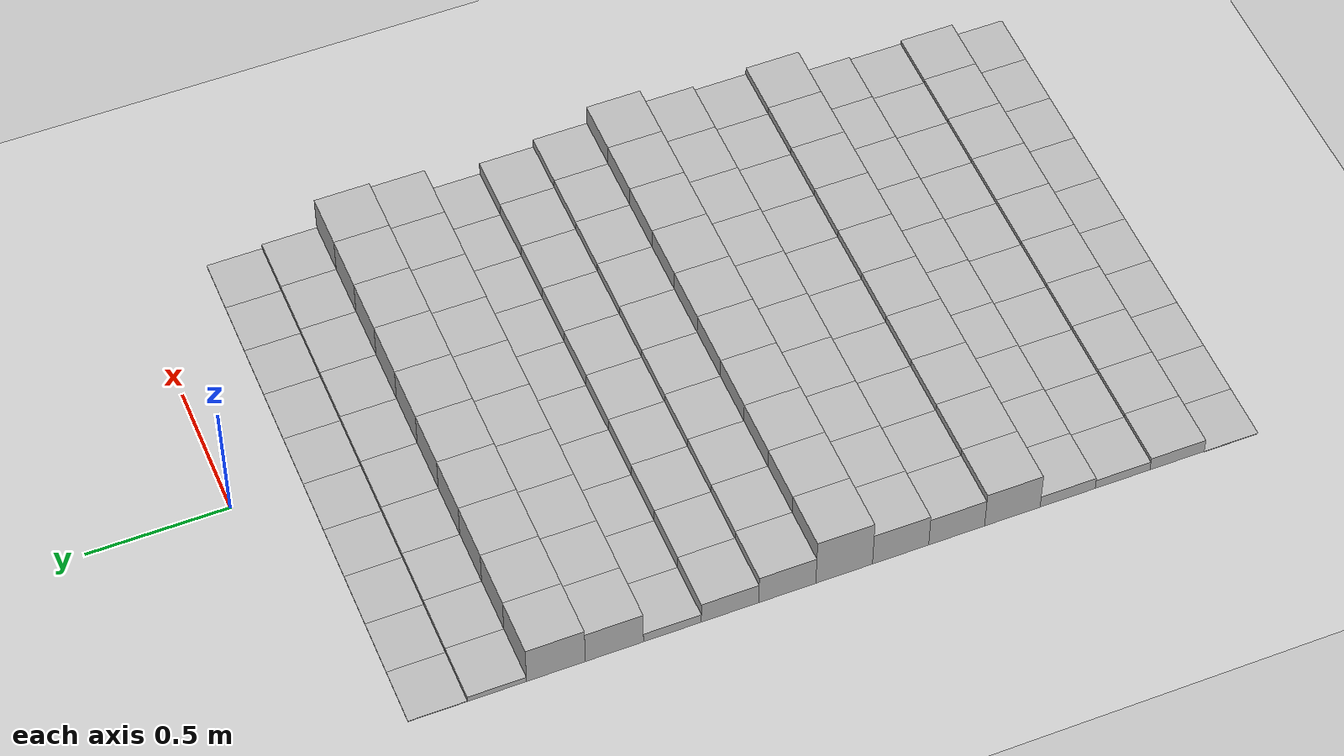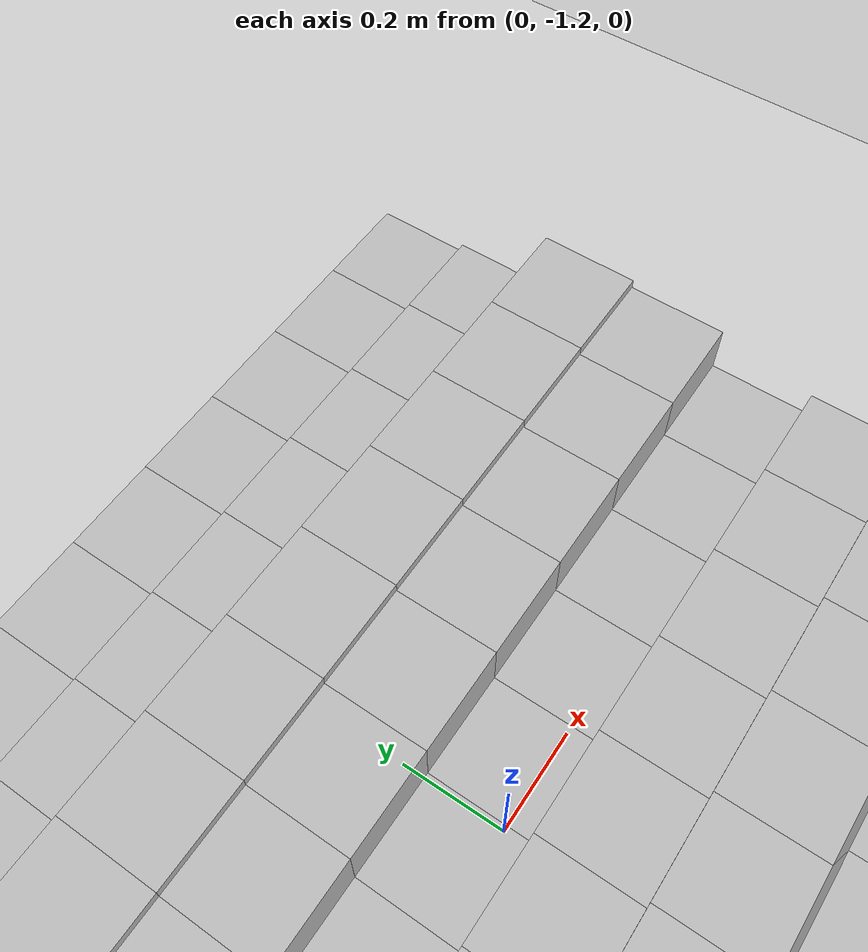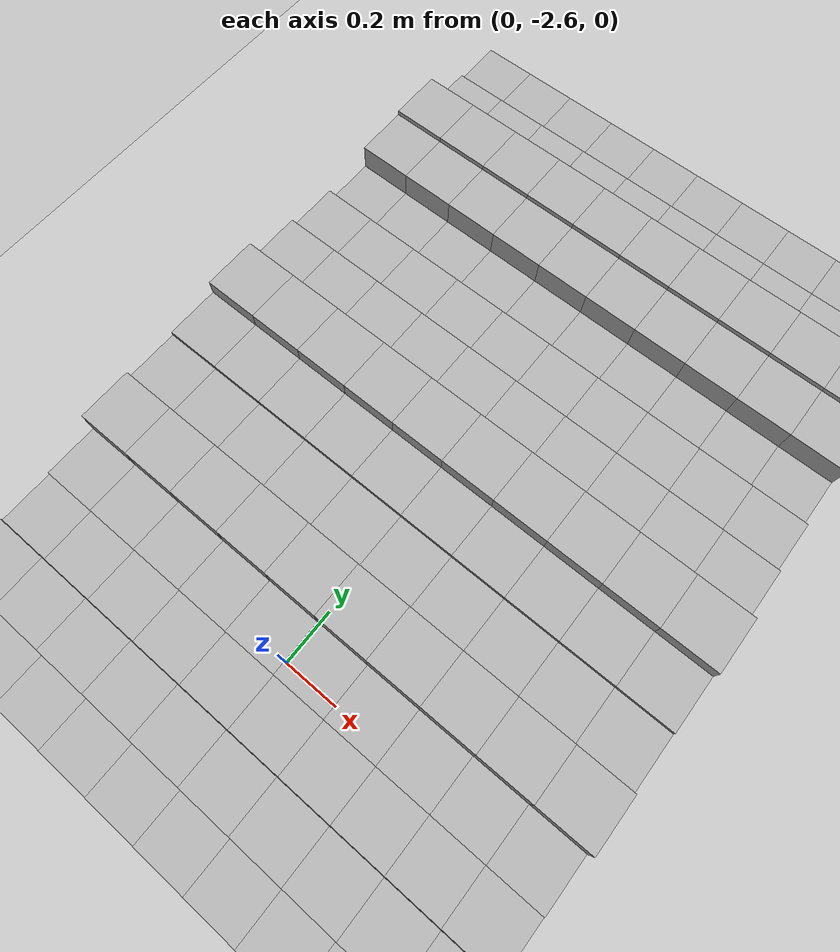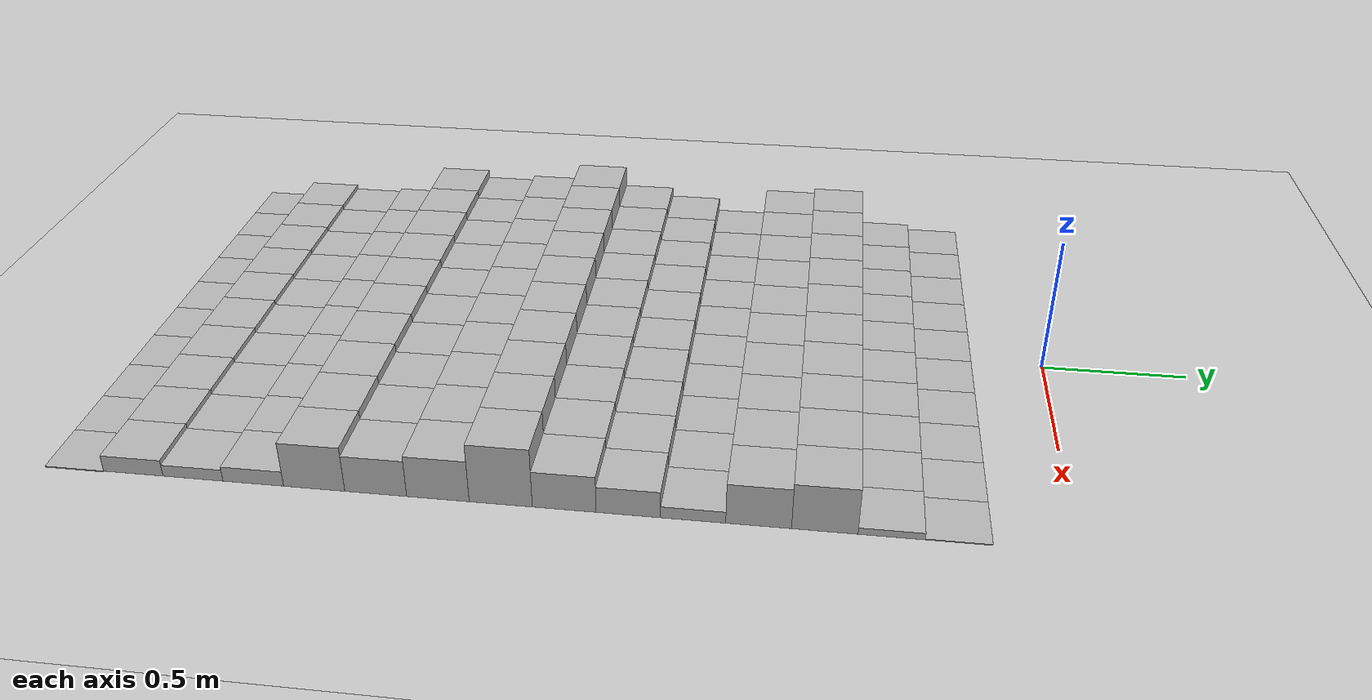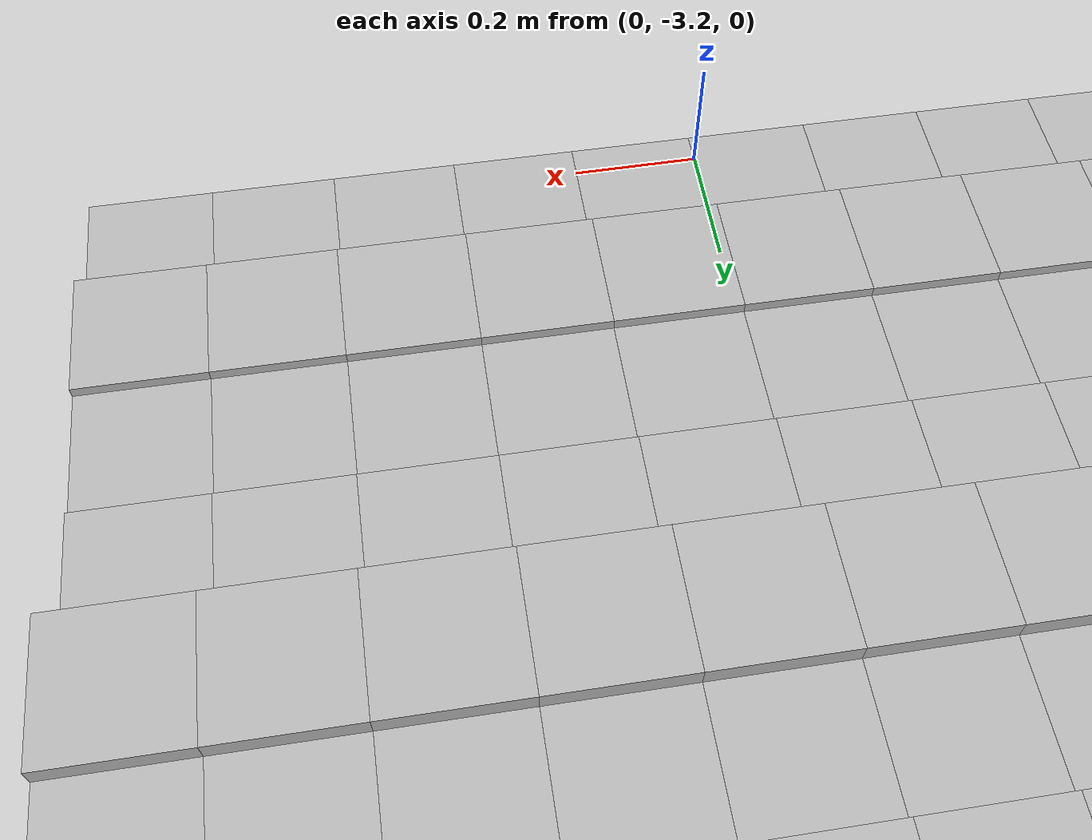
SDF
<?xml version="1.0" ?>
<sdf version="1.6">
  <world name="default">
  <gravity>0 0 -9.81</gravity>
  <physics name="ode_900iters" type="ode" default="true">
    <!-- the combination of 2 params below provides real time factor speed for simulation -->
    <!-- max_real_time_factor = real_time_update_rate * max_step_size -->
    <!-- min_real_time_factor depends only from max_step_size -->
    <real_time_update_rate>1000</real_time_update_rate>
    <max_step_size>0.003 </max_step_size>
      <ode>
        <solver>
          <type>quick</type>
          <iters>900</iters>
        <sor>0.9</sor>
        </solver>
      </ode>
    </physics>
      <include>
      <uri>model://ground_plane</uri>
    </include>
    <include>
      <uri>model://sun</uri>
    </include>
        <include>
		<uri>model://strirus_ga_body_optimization/maps/Generated_terrain_2</uri>
      <name>Terrain</name>
      <pose>0 -0.35 0 0 0 0</pose>
    </include>
  </world>
</sdf>

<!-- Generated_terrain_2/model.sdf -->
<sdf version='1.6'>
	<model name='Terrain'>
		<static>true</static>
		<link name="box_0_0">
			<pose>-0.9 0.0 0.00155699473406 0 0 0</pose>
			<inertial>
				<mass>1.0</mass>
				<inertia>
					<ixx>0.0</ixx>
 					<ixy>0.0</ixy>
   					<ixz>0.0</ixz>
   					<iyy>0.0</iyy>
 					<iyz>0.0</iyz>
   					<izz>0.0</izz>
 				</inertia>
			</inertial>
			<collision name="collision">
				<geometry>
					<box>
						<size>0.2 0.2 0.00311398946811</size>
					</box>
				</geometry>
			</collision>
			<visual name="visual">
				<geometry>
					<box>
						<size>0.2 0.2 0.00311398946811</size>
					</box>
				</geometry>
			</visual>
		</link>

		<link name="box_0_1">
			<pose>-0.7 0.0 0.00155699473406 0 0 0</pose>
			<inertial>
				<mass>1.0</mass>
				<inertia>
					<ixx>0.0</ixx>
 					<ixy>0.0</ixy>
   					<ixz>0.0</ixz>
   					<iyy>0.0</iyy>
 					<iyz>0.0</iyz>
   					<izz>0.0</izz>
 				</inertia>
			</inertial>
			<collision name="collision">
				<geometry>
					<box>
						<size>0.2 0.2 0.00311398946811</size>
					</box>
				</geometry>
			</collision>
			<visual name="visual">
				<geometry>
					<box>
						<size>0.2 0.2 0.00311398946811</size>
					</box>
				</geometry>
			</visual>
		</link>

		<link name="box_0_2">
			<pose>-0.5 0.0 0.00155699473406 0 0 0</pose>
			<inertial>
				<mass>1.0</mass>
				<inertia>
					<ixx>0.0</ixx>
 					<ixy>0.0</ixy>
   					<ixz>0.0</ixz>
   					<iyy>0.0</iyy>
 					<iyz>0.0</iyz>
   					<izz>0.0</izz>
 				</inertia>
			</inertial>
			<collision name="collision">
				<geometry>
					<box>
						<size>0.2 0.2 0.00311398946811</size>
					</box>
				</geometry>
			</collision>
			<visual name="visual">
				<geometry>
					<box>
						<size>0.2 0.2 0.00311398946811</size>
					</box>
				</geometry>
			</visual>
		</link>

		<link name="box_0_3">
			<pose>-0.3 0.0 0.00155699473406 0 0 0</pose>
			<inertial>
				<mass>1.0</mass>
				<inertia>
					<ixx>0.0</ixx>
 					<ixy>0.0</ixy>
   					<ixz>0.0</ixz>
   					<iyy>0.0</iyy>
 					<iyz>0.0</iyz>
   					<izz>0.0</izz>
 				</inertia>
			</inertial>
			<collision name="collision">
				<geometry>
					<box>
						<size>0.2 0.2 0.00311398946811</size>
					</box>
				</geometry>
			</collision>
			<visual name="visual">
				<geometry>
					<box>
						<size>0.2 0.2 0.00311398946811</size>
					</box>
				</geometry>
			</visual>
		</link>

		<link name="box_0_4">
			<pose>-0.1 0.0 0.00155699473406 0 0 0</pose>
			<inertial>
				<mass>1.0</mass>
				<inertia>
					<ixx>0.0</ixx>
 					<ixy>0.0</ixy>
   					<ixz>0.0</ixz>
   					<iyy>0.0</iyy>
 					<iyz>0.0</iyz>
   					<izz>0.0</izz>
 				</inertia>
			</inertial>
			<collision name="collision">
				<geometry>
					<box>
						<size>0.2 0.2 0.00311398946811</size>
					</box>
				</geometry>
			</collision>
			<visual name="visual">
				<geometry>
					<box>
						<size>0.2 0.2 0.00311398946811</size>
					</box>
				</geometry>
			</visual>
		</link>

		<link name="box_0_5">
			<pose>0.1 0.0 0.00155699473406 0 0 0</pose>
			<inertial>
				<mass>1.0</mass>
				<inertia>
					<ixx>0.0</ixx>
 					<ixy>0.0</ixy>
   					<ixz>0.0</ixz>
   					<iyy>0.0</iyy>
 					<iyz>0.0</iyz>
   					<izz>0.0</izz>
 				</inertia>
			</inertial>
			<collision name="collision">
				<geometry>
					<box>
						<size>0.2 0.2 0.00311398946811</size>
					</box>
				</geometry>
			</collision>
			<visual name="visual">
				<geometry>
					<box>
						<size>0.2 0.2 0.00311398946811</size>
					</box>
				</geometry>
			</visual>
		</link>

		<link name="box_0_6">
			<pose>0.3 0.0 0.00155699473406 0 0 0</pose>
			<inertial>
				<mass>1.0</mass>
				<inertia>
					<ixx>0.0</ixx>
 					<ixy>0.0</ixy>
   					<ixz>0.0</ixz>
   					<iyy>0.0</iyy>
 					<iyz>0.0</iyz>
   					<izz>0.0</izz>
 				</inertia>
			</inertial>
			<collision name="collision">
				<geometry>
					<box>
						<size>0.2 0.2 0.00311398946811</size>
					</box>
				</geometry>
			</collision>
			<visual name="visual">
				<geometry>
					<box>
						<size>0.2 0.2 0.00311398946811</size>
					</box>
				</geometry>
			</visual>
		</link>

		<link name="box_0_7">
			<pose>0.5 0.0 0.00155699473406 0 0 0</pose>
			<inertial>
				<mass>1.0</mass>
				<inertia>
					<ixx>0.0</ixx>
 					<ixy>0.0</ixy>
   					<ixz>0.0</ixz>
   					<iyy>0.0</iyy>
 					<iyz>0.0</iyz>
   					<izz>0.0</izz>
 				</inertia>
			</inertial>
			<collision name="collision">
				<geometry>
					<box>
						<size>0.2 0.2 0.00311398946811</size>
					</box>
				</geometry>
			</collision>
			<visual name="visual">
				<geometry>
					<box>
						<size>0.2 0.2 0.00311398946811</size>
					</box>
				</geometry>
			</visual>
		</link>

		<link name="box_0_8">
			<pose>0.7 0.0 0.00155699473406 0 0 0</pose>
			<inertial>
				<mass>1.0</mass>
				<inertia>
					<ixx>0.0</ixx>
 					<ixy>0.0</ixy>
   					<ixz>0.0</ixz>
   					<iyy>0.0</iyy>
 					<iyz>0.0</iyz>
   					<izz>0.0</izz>
 				</inertia>
			</inertial>
			<collision name="collision">
				<geometry>
					<box>
						<size>0.2 0.2 0.00311398946811</size>
					</box>
				</geometry>
			</collision>
			<visual name="visual">
				<geometry>
					<box>
						<size>0.2 0.2 0.00311398946811</size>
					</box>
				</geometry>
			</visual>
		</link>

		<link name="box_0_9">
			<pose>0.9 0.0 0.00155699473406 0 0 0</pose>
			<inertial>
				<mass>1.0</mass>
				<inertia>
					<ixx>0.0</ixx>
 					<ixy>0.0</ixy>
   					<ixz>0.0</ixz>
   					<iyy>0.0</iyy>
 					<iyz>0.0</iyz>
   					<izz>0.0</izz>
 				</inertia>
			</inertial>
			<collision name="collision">
				<geometry>
					<box>
						<size>0.2 0.2 0.00311398946811</size>
					</box>
				</geometry>
			</collision>
			<visual name="visual">
				<geometry>
					<box>
						<size>0.2 0.2 0.00311398946811</size>
					</box>
				</geometry>
			</visual>
		</link>

		<link name="box_1_0">
			<pose>-0.9 -0.2 0.012157828828 0 0 0</pose>
			<inertial>
				<mass>1.0</mass>
				<inertia>
					<ixx>0.0</ixx>
 					<ixy>0.0</ixy>
   					<ixz>0.0</ixz>
   					<iyy>0.0</iyy>
 					<iyz>0.0</iyz>
   					<izz>0.0</izz>
 				</inertia>
			</inertial>
			<collision name="collision">
				<geometry>
					<box>
						<size>0.2 0.2 0.0243156576561</size>
					</box>
				</geometry>
			</collision>
			<visual name="visual">
				<geometry>
					<box>
						<size>0.2 0.2 0.0243156576561</size>
					</box>
				</geometry>
			</visual>
		</link>

		<link name="box_1_1">
			<pose>-0.7 -0.2 0.012157828828 0 0 0</pose>
			<inertial>
				<mass>1.0</mass>
				<inertia>
					<ixx>0.0</ixx>
 					<ixy>0.0</ixy>
   					<ixz>0.0</ixz>
   					<iyy>0.0</iyy>
 					<iyz>0.0</iyz>
   					<izz>0.0</izz>
 				</inertia>
			</inertial>
			<collision name="collision">
				<geometry>
					<box>
						<size>0.2 0.2 0.0243156576561</size>
					</box>
				</geometry>
			</collision>
			<visual name="visual">
				<geometry>
					<box>
						<size>0.2 0.2 0.0243156576561</size>
					</box>
				</geometry>
			</visual>
		</link>

		<link name="box_1_2">
			<pose>-0.5 -0.2 0.012157828828 0 0 0</pose>
			<inertial>
				<mass>1.0</mass>
				<inertia>
					<ixx>0.0</ixx>
 					<ixy>0.0</ixy>
   					<ixz>0.0</ixz>
   					<iyy>0.0</iyy>
 					<iyz>0.0</iyz>
   					<izz>0.0</izz>
 				</inertia>
			</inertial>
			<collision name="collision">
				<geometry>
					<box>
						<size>0.2 0.2 0.0243156576561</size>
					</box>
				</geometry>
			</collision>
			<visual name="visual">
				<geometry>
					<box>
						<size>0.2 0.2 0.0243156576561</size>
					</box>
				</geometry>
			</visual>
		</link>

		<link name="box_1_3">
			<pose>-0.3 -0.2 0.012157828828 0 0 0</pose>
			<inertial>
				<mass>1.0</mass>
				<inertia>
					<ixx>0.0</ixx>
 					<ixy>0.0</ixy>
   					<ixz>0.0</ixz>
   					<iyy>0.0</iyy>
 					<iyz>0.0</iyz>
   					<izz>0.0</izz>
 				</inertia>
			</inertial>
			<collision name="collision">
				<geometry>
					<box>
						<size>0.2 0.2 0.0243156576561</size>
					</box>
				</geometry>
			</collision>
			<visual name="visual">
				<geometry>
					<box>
						<size>0.2 0.2 0.0243156576561</size>
					</box>
				</geometry>
			</visual>
		</link>

		<link name="box_1_4">
			<pose>-0.1 -0.2 0.012157828828 0 0 0</pose>
			<inertial>
				<mass>1.0</mass>
				<inertia>
					<ixx>0.0</ixx>
 					<ixy>0.0</ixy>
   					<ixz>0.0</ixz>
   					<iyy>0.0</iyy>
 					<iyz>0.0</iyz>
   					<izz>0.0</izz>
 				</inertia>
			</inertial>
			<collision name="collision">
				<geometry>
					<box>
						<size>0.2 0.2 0.0243156576561</size>
					</box>
				</geometry>
			</collision>
			<visual name="visual">
				<geometry>
					<box>
						<size>0.2 0.2 0.0243156576561</size>
					</box>
				</geometry>
			</visual>
		</link>

		<link name="box_1_5">
			<pose>0.1 -0.2 0.012157828828 0 0 0</pose>
			<inertial>
				<mass>1.0</mass>
				<inertia>
					<ixx>0.0</ixx>
 					<ixy>0.0</ixy>
   					<ixz>0.0</ixz>
   					<iyy>0.0</iyy>
 					<iyz>0.0</iyz>
   					<izz>0.0</izz>
 				</inertia>
			</inertial>
			<collision name="collision">
				<geometry>
					<box>
						<size>0.2 0.2 0.0243156576561</size>
					</box>
				</geometry>
			</collision>
			<visual name="visual">
				<geometry>
					<box>
						<size>0.2 0.2 0.0243156576561</size>
					</box>
				</geometry>
			</visual>
		</link>

		<link name="box_1_6">
			<pose>0.3 -0.2 0.012157828828 0 0 0</pose>
			<inertial>
				<mass>1.0</mass>
				<inertia>
					<ixx>0.0</ixx>
 					<ixy>0.0</ixy>
   					<ixz>0.0</ixz>
   					<iyy>0.0</iyy>
 					<iyz>0.0</iyz>
   					<izz>0.0</izz>
 				</inertia>
			</inertial>
			<collision name="collision">
				<geometry>
					<box>
						<size>0.2 0.2 0.0243156576561</size>
					</box>
				</geometry>
			</collision>
			<visual name="visual">
				<geometry>
					<box>
						<size>0.2 0.2 0.0243156576561</size>
					</box>
				</geometry>
			</visual>
		</link>

		<link name="box_1_7">
			<pose>0.5 -0.2 0.012157828828 0 0 0</pose>
			<inertial>
				<mass>1.0</mass>
				<inertia>
					<ixx>0.0</ixx>
 					<ixy>0.0</ixy>
   					<ixz>0.0</ixz>
   					<iyy>0.0</iyy>
 					<iyz>0.0</iyz>
   					<izz>0.0</izz>
 				</inertia>
			</inertial>
			<collision name="collision">
				<geometry>
					<box>
						<size>0.2 0.2 0.0243156576561</size>
					</box>
				</geometry>
			</collision>
			<visual name="visual">
				<geometry>
					<box>
						<size>0.2 0.2 0.0243156576561</size>
					</box>
				</geometry>
			</visual>
		</link>

		<link name="box_1_8">
			<pose>0.7 -0.2 0.012157828828 0 0 0</pose>
			<inertial>
				<mass>1.0</mass>
				<inertia>
					<ixx>0.0</ixx>
 					<ixy>0.0</ixy>
   					<ixz>0.0</ixz>
   					<iyy>0.0</iyy>
 					<iyz>0.0</iyz>
   					<izz>0.0</izz>
 				</inertia>
			</inertial>
			<collision name="collision">
				<geometry>
					<box>
						<size>0.2 0.2 0.0243156576561</size>
					</box>
				</geometry>
			</collision>
			<visual name="visual">
				<geometry>
					<box>
						<size>0.2 0.2 0.0243156576561</size>
					</box>
				</geometry>
			</visual>
		</link>

		<link name="box_1_9">
			<pose>0.9 -0.2 0.012157828828 0 0 0</pose>
			<inertial>
				<mass>1.0</mass>
				<inertia>
					<ixx>0.0</ixx>
 					<ixy>0.0</ixy>
   					<ixz>0.0</ixz>
   					<iyy>0.0</iyy>
 					<iyz>0.0</iyz>
   					<izz>0.0</izz>
 				</inertia>
			</inertial>
			<collision name="collision">
				<geometry>
					<box>
						<size>0.2 0.2 0.0243156576561</size>
					</box>
				</geometry>
			</collision>
			<visual name="visual">
				<geometry>
					<box>
						<size>0.2 0.2 0.0243156576561</size>
					</box>
				</geometry>
			</visual>
		</link>

		<link name="box_2_0">
			<pose>-0.9 -0.4 0.0843452902133 0 0 0</pose>
			<inertial>
				<mass>1.0</mass>
				<inertia>
					<ixx>0.0</ixx>
 					<ixy>0.0</ixy>
   					<ixz>0.0</ixz>
   					<iyy>0.0</iyy>
 					<iyz>0.0</iyz>
   					<izz>0.0</izz>
 				</inertia>
			</inertial>
			<collision name="collision">
				<geometry>
					<box>
						<size>0.2 0.2 0.168690580427</size>
					</box>
				</geometry>
			</collision>
			<visual name="visual">
				<geometry>
					<box>
						<size>0.2 0.2 0.168690580427</size>
					</box>
				</geometry>
			</visual>
		</link>

		<link name="box_2_1">
			<pose>-0.7 -0.4 0.0843452902133 0 0 0</pose>
			<inertial>
				<mass>1.0</mass>
				<inertia>
					<ixx>0.0</ixx>
 					<ixy>0.0</ixy>
   					<ixz>0.0</ixz>
   					<iyy>0.0</iyy>
 					<iyz>0.0</iyz>
   					<izz>0.0</izz>
 				</inertia>
			</inertial>
			<collision name="collision">
				<geometry>
					<box>
						<size>0.2 0.2 0.168690580427</size>
					</box>
				</geometry>
			</collision>
			<visual name="visual">
				<geometry>
					<box>
						<size>0.2 0.2 0.168690580427</size>
					</box>
				</geometry>
			</visual>
		</link>

		<link name="box_2_2">
			<pose>-0.5 -0.4 0.0843452902133 0 0 0</pose>
			<inertial>
				<mass>1.0</mass>
				<inertia>
					<ixx>0.0</ixx>
 					<ixy>0.0</ixy>
   					<ixz>0.0</ixz>
   					<iyy>0.0</iyy>
 					<iyz>0.0</iyz>
   					<izz>0.0</izz>
 				</inertia>
			</inertial>
			<collision name="collision">
				<geometry>
					<box>
						<size>0.2 0.2 0.168690580427</size>
					</box>
				</geometry>
			</collision>
			<visual name="visual">
				<geometry>
					<box>
						<size>0.2 0.2 0.168690580427</size>
					</box>
				</geometry>
			</visual>
		</link>

		<link name="box_2_3">
			<pose>-0.3 -0.4 0.0843452902133 0 0 0</pose>
			<inertial>
				<mass>1.0</mass>
				<inertia>
					<ixx>0.0</ixx>
 					<ixy>0.0</ixy>
   					<ixz>0.0</ixz>
   					<iyy>0.0</iyy>
 					<iyz>0.0</iyz>
   					<izz>0.0</izz>
 				</inertia>
			</inertial>
			<collision name="collision">
				<geometry>
					<box>
						<size>0.2 0.2 0.168690580427</size>
					</box>
				</geometry>
			</collision>
			<visual name="visual">
				<geometry>
					<box>
						<size>0.2 0.2 0.168690580427</size>
					</box>
				</geometry>
			</visual>
		</link>

		<link name="box_2_4">
			<pose>-0.1 -0.4 0.0843452902133 0 0 0</pose>
			<inertial>
				<mass>1.0</mass>
				<inertia>
					<ixx>0.0</ixx>
 					<ixy>0.0</ixy>
   					<ixz>0.0</ixz>
   					<iyy>0.0</iyy>
 					<iyz>0.0</iyz>
   					<izz>0.0</izz>
 				</inertia>
			</inertial>
			<collision name="collision">
				<geometry>
					<box>
						<size>0.2 0.2 0.168690580427</size>
					</box>
				</geometry>
			</collision>
			<visual name="visual">
				<geometry>
					<box>
						<size>0.2 0.2 0.168690580427</size>
					</box>
				</geometry>
			</visual>
		</link>

		<link name="box_2_5">
			<pose>0.1 -0.4 0.0843452902133 0 0 0</pose>
			<inertial>
				<mass>1.0</mass>
				<inertia>
					<ixx>0.0</ixx>
 					<ixy>0.0</ixy>
   					<ixz>0.0</ixz>
   					<iyy>0.0</iyy>
 					<iyz>0.0</iyz>
   					<izz>0.0</izz>
 				</inertia>
			</inertial>
			<collision name="collision">
				<geometry>
					<box>
						<size>0.2 0.2 0.168690580427</size>
					</box>
				</geometry>
			</collision>
			<visual name="visual">
				<geometry>
					<box>
						<size>0.2 0.2 0.168690580427</size>
					</box>
				</geometry>
			</visual>
		</link>

		<link name="box_2_6">
			<pose>0.3 -0.4 0.0843452902133 0 0 0</pose>
			<inertial>
				<mass>1.0</mass>
				<inertia>
					<ixx>0.0</ixx>
 					<ixy>0.0</ixy>
   					<ixz>0.0</ixz>
   					<iyy>0.0</iyy>
 					<iyz>0.0</iyz>
   					<izz>0.0</izz>
 				</inertia>
			</inertial>
			<collision name="collision">
				<geometry>
					<box>
						<size>0.2 0.2 0.168690580427</size>
					</box>
				</geometry>
			</collision>
			<visual name="visual">
				<geometry>
					<box>
						<size>0.2 0.2 0.168690580427</size>
					</box>
				</geometry>
			</visual>
		</link>

		<link name="box_2_7">
			<pose>0.5 -0.4 0.0843452902133 0 0 0</pose>
			<inertial>
				<mass>1.0</mass>
				<inertia>
					<ixx>0.0</ixx>
 					<ixy>0.0</ixy>
   					<ixz>0.0</ixz>
   					<iyy>0.0</iyy>
 					<iyz>0.0</iyz>
   					<izz>0.0</izz>
 				</inertia>
			</inertial>
			<collision name="collision">
				<geometry>
					<box>
						<size>0.2 0.2 0.168690580427</size>
					</box>
				</geometry>
			</collision>
			<visual name="visual">
				<geometry>
					<box>
						<size>0.2 0.2 0.168690580427</size>
					</box>
				</geometry>
			</visual>
		</link>

		<link name="box_2_8">
			<pose>0.7 -0.4 0.0843452902133 0 0 0</pose>
			<inertial>
				<mass>1.0</mass>
				<inertia>
					<ixx>0.0</ixx>
 					<ixy>0.0</ixy>
   					<ixz>0.0</ixz>
   					<iyy>0.0</iyy>
 					<iyz>0.0</iyz>
   					<izz>0.0</izz>
 				</inertia>
			</inertial>
			<collision name="collision">
				<geometry>
					<box>
						<size>0.2 0.2 0.168690580427</size>
					</box>
				</geometry>
			</collision>
			<visual name="visual">
				<geometry>
					<box>
						<size>0.2 0.2 0.168690580427</size>
					</box>
				</geometry>
			</visual>
		</link>

		<link name="box_2_9">
			<pose>0.9 -0.4 0.0843452902133 0 0 0</pose>
			<inertial>
				<mass>1.0</mass>
				<inertia>
					<ixx>0.0</ixx>
 					<ixy>0.0</ixy>
   					<ixz>0.0</ixz>
   					<iyy>0.0</iyy>
 					<iyz>0.0</iyz>
   					<izz>0.0</izz>
 				</inertia>
			</inertial>
			<collision name="collision">
				<geometry>
					<box>
						<size>0.2 0.2 0.168690580427</size>
					</box>
				</geometry>
			</collision>
			<visual name="visual">
				<geometry>
					<box>
						<size>0.2 0.2 0.168690580427</size>
					</box>
				</geometry>
			</visual>
		</link>

		<link name="box_3_0">
			<pose>-0.9 -0.6 0.0744343411689 0 0 0</pose>
			<inertial>
				<mass>1.0</mass>
				<inertia>
					<ixx>0.0</ixx>
 					<ixy>0.0</ixy>
   					<ixz>0.0</ixz>
   					<iyy>0.0</iyy>
 					<iyz>0.0</iyz>
   					<izz>0.0</izz>
 				</inertia>
			</inertial>
			<collision name="collision">
				<geometry>
					<box>
						<size>0.2 0.2 0.148868682338</size>
					</box>
				</geometry>
			</collision>
			<visual name="visual">
				<geometry>
					<box>
						<size>0.2 0.2 0.148868682338</size>
					</box>
				</geometry>
			</visual>
		</link>

		<link name="box_3_1">
			<pose>-0.7 -0.6 0.0744343411689 0 0 0</pose>
			<inertial>
				<mass>1.0</mass>
				<inertia>
					<ixx>0.0</ixx>
 					<ixy>0.0</ixy>
   					<ixz>0.0</ixz>
   					<iyy>0.0</iyy>
 					<iyz>0.0</iyz>
   					<izz>0.0</izz>
 				</inertia>
			</inertial>
			<collision name="collision">
				<geometry>
					<box>
						<size>0.2 0.2 0.148868682338</size>
					</box>
				</geometry>
			</collision>
			<visual name="visual">
				<geometry>
					<box>
						<size>0.2 0.2 0.148868682338</size>
					</box>
				</geometry>
			</visual>
		</link>

		<link name="box_3_2">
			<pose>-0.5 -0.6 0.0744343411689 0 0 0</pose>
			<inertial>
				<mass>1.0</mass>
				<inertia>
					<ixx>0.0</ixx>
 					<ixy>0.0</ixy>
   					<ixz>0.0</ixz>
   					<iyy>0.0</iyy>
 					<iyz>0.0</iyz>
   					<izz>0.0</izz>
 				</inertia>
			</inertial>
			<collision name="collision">
				<geometry>
					<box>
						<size>0.2 0.2 0.148868682338</size>
					</box>
				</geometry>
			</collision>
			<visual name="visual">
				<geometry>
					<box>
						<size>0.2 0.2 0.148868682338</size>
					</box>
				</geometry>
			</visual>
		</link>

		<link name="box_3_3">
			<pose>-0.3 -0.6 0.0744343411689 0 0 0</pose>
			<inertial>
				<mass>1.0</mass>
				<inertia>
					<ixx>0.0</ixx>
 					<ixy>0.0</ixy>
   					<ixz>0.0</ixz>
   					<iyy>0.0</iyy>
 					<iyz>0.0</iyz>
   					<izz>0.0</izz>
 				</inertia>
			</inertial>
			<collision name="collision">
				<geometry>
					<box>
						<size>0.2 0.2 0.148868682338</size>
					</box>
				</geometry>
			</collision>
			<visual name="visual">
				<geometry>
					<box>
						<size>0.2 0.2 0.148868682338</size>
					</box>
				</geometry>
			</visual>
		</link>

		<link name="box_3_4">
			<pose>-0.1 -0.6 0.0744343411689 0 0 0</pose>
			<inertial>
				<mass>1.0</mass>
				<inertia>
					<ixx>0.0</ixx>
 					<ixy>0.0</ixy>
   					<ixz>0.0</ixz>
   					<iyy>0.0</iyy>
 					<iyz>0.0</iyz>
   					<izz>0.0</izz>
 				</inertia>
			</inertial>
			<collision name="collision">
				<geometry>
					<box>
						<size>0.2 0.2 0.148868682338</size>
					</box>
				</geometry>
			</collision>
			<visual name="visual">
				<geometry>
					<box>
						<size>0.2 0.2 0.148868682338</size>
					</box>
				</geometry>
			</visual>
		</link>

		<link name="box_3_5">
			<pose>0.1 -0.6 0.0744343411689 0 0 0</pose>
			<inertial>
				<mass>1.0</mass>
				<inertia>
					<ixx>0.0</ixx>
 					<ixy>0.0</ixy>
   					<ixz>0.0</ixz>
   					<iyy>0.0</iyy>
 					<iyz>0.0</iyz>
   					<izz>0.0</izz>
 				</inertia>
			</inertial>
			<collision name="collision">
				<geometry>
					<box>
						<size>0.2 0.2 0.148868682338</size>
					</box>
				</geometry>
			</collision>
			<visual name="visual">
				<geometry>
					<box>
						<size>0.2 0.2 0.148868682338</size>
					</box>
				</geometry>
			</visual>
		</link>

		<link name="box_3_6">
			<pose>0.3 -0.6 0.0744343411689 0 0 0</pose>
			<inertial>
				<mass>1.0</mass>
				<inertia>
					<ixx>0.0</ixx>
 					<ixy>0.0</ixy>
   					<ixz>0.0</ixz>
   					<iyy>0.0</iyy>
 					<iyz>0.0</iyz>
   					<izz>0.0</izz>
 				</inertia>
			</inertial>
			<collision name="collision">
				<geometry>
					<box>
						<size>0.2 0.2 0.148868682338</size>
					</box>
				</geometry>
			</collision>
			<visual name="visual">
				<geometry>
					<box>
						<size>0.2 0.2 0.148868682338</size>
					</box>
				</geometry>
			</visual>
		</link>

		<link name="box_3_7">
			<pose>0.5 -0.6 0.0744343411689 0 0 0</pose>
			<inertial>
				<mass>1.0</mass>
				<inertia>
					<ixx>0.0</ixx>
 					<ixy>0.0</ixy>
   					<ixz>0.0</ixz>
   					<iyy>0.0</iyy>
 					<iyz>0.0</iyz>
   					<izz>0.0</izz>
 				</inertia>
			</inertial>
			<collision name="collision">
				<geometry>
					<box>
						<size>0.2 0.2 0.148868682338</size>
					</box>
				</geometry>
			</collision>
			<visual name="visual">
				<geometry>
					<box>
						<size>0.2 0.2 0.148868682338</size>
					</box>
				</geometry>
			</visual>
		</link>

		<link name="box_3_8">
			<pose>0.7 -0.6 0.0744343411689 0 0 0</pose>
			<inertial>
				<mass>1.0</mass>
				<inertia>
					<ixx>0.0</ixx>
 					<ixy>0.0</ixy>
   					<ixz>0.0</ixz>
   					<iyy>0.0</iyy>
 					<iyz>0.0</iyz>
   					<izz>0.0</izz>
 				</inertia>
			</inertial>
			<collision name="collision">
				<geometry>
					<box>
						<size>0.2 0.2 0.148868682338</size>
					</box>
				</geometry>
			</collision>
			<visual name="visual">
				<geometry>
					<box>
						<size>0.2 0.2 0.148868682338</size>
					</box>
				</geometry>
			</visual>
		</link>

		<link name="box_3_9">
			<pose>0.9 -0.6 0.0744343411689 0 0 0</pose>
			<inertial>
				<mass>1.0</mass>
				<inertia>
					<ixx>0.0</ixx>
 					<ixy>0.0</ixy>
   					<ixz>0.0</ixz>
   					<iyy>0.0</iyy>
 					<iyz>0.0</iyz>
   					<izz>0.0</izz>
 				</inertia>
			</inertial>
			<collision name="collision">
				<geometry>
					<box>
						<size>0.2 0.2 0.148868682338</size>
					</box>
				</geometry>
			</collision>
			<visual name="visual">
				<geometry>
					<box>
						<size>0.2 0.2 0.148868682338</size>
					</box>
				</geometry>
			</visual>
		</link>

		<link name="box_4_0">
			<pose>-0.9 -0.8 0.0211775174678 0 0 0</pose>
			<inertial>
				<mass>1.0</mass>
				<inertia>
					<ixx>0.0</ixx>
 					<ixy>0.0</ixy>
   					<ixz>0.0</ixz>
   					<iyy>0.0</iyy>
 					<iyz>0.0</iyz>
   					<izz>0.0</izz>
 				</inertia>
			</inertial>
			<collision name="collision">
				<geometry>
					<box>
						<size>0.2 0.2 0.0423550349355</size>
					</box>
				</geometry>
			</collision>
			<visual name="visual">
				<geometry>
					<box>
						<size>0.2 0.2 0.0423550349355</size>
					</box>
				</geometry>
			</visual>
		</link>

		<link name="box_4_1">
			<pose>-0.7 -0.8 0.0211775174678 0 0 0</pose>
			<inertial>
				<mass>1.0</mass>
				<inertia>
					<ixx>0.0</ixx>
 					<ixy>0.0</ixy>
   					<ixz>0.0</ixz>
   					<iyy>0.0</iyy>
 					<iyz>0.0</iyz>
   					<izz>0.0</izz>
 				</inertia>
			</inertial>
			<collision name="collision">
				<geometry>
					<box>
						<size>0.2 0.2 0.0423550349355</size>
					</box>
				</geometry>
			</collision>
			<visual name="visual">
				<geometry>
					<box>
						<size>0.2 0.2 0.0423550349355</size>
					</box>
				</geometry>
			</visual>
		</link>

		<link name="box_4_2">
			<pose>-0.5 -0.8 0.0211775174678 0 0 0</pose>
			<inertial>
				<mass>1.0</mass>
				<inertia>
					<ixx>0.0</ixx>
 					<ixy>0.0</ixy>
   					<ixz>0.0</ixz>
   					<iyy>0.0</iyy>
 					<iyz>0.0</iyz>
   					<izz>0.0</izz>
 				</inertia>
			</inertial>
			<collision name="collision">
				<geometry>
					<box>
						<size>0.2 0.2 0.0423550349355</size>
					</box>
				</geometry>
			</collision>
			<visual name="visual">
				<geometry>
					<box>
						<size>0.2 0.2 0.0423550349355</size>
					</box>
				</geometry>
			</visual>
		</link>

		<link name="box_4_3">
			<pose>-0.3 -0.8 0.0211775174678 0 0 0</pose>
			<inertial>
				<mass>1.0</mass>
				<inertia>
					<ixx>0.0</ixx>
 					<ixy>0.0</ixy>
   					<ixz>0.0</ixz>
   					<iyy>0.0</iyy>
 					<iyz>0.0</iyz>
   					<izz>0.0</izz>
 				</inertia>
			</inertial>
			<collision name="collision">
				<geometry>
					<box>
						<size>0.2 0.2 0.0423550349355</size>
					</box>
				</geometry>
			</collision>
			<visual name="visual">
				<geometry>
					<box>
						<size>0.2 0.2 0.0423550349355</size>
					</box>
				</geometry>
			</visual>
		</link>

		<link name="box_4_4">
			<pose>-0.1 -0.8 0.0211775174678 0 0 0</pose>
			<inertial>
				<mass>1.0</mass>
				<inertia>
					<ixx>0.0</ixx>
 					<ixy>0.0</ixy>
   					<ixz>0.0</ixz>
   					<iyy>0.0</iyy>
 					<iyz>0.0</iyz>
   					<izz>0.0</izz>
 				</inertia>
			</inertial>
			<collision name="collision">
				<geometry>
					<box>
						<size>0.2 0.2 0.0423550349355</size>
					</box>
				</geometry>
			</collision>
			<visual name="visual">
				<geometry>
					<box>
						<size>0.2 0.2 0.0423550349355</size>
					</box>
				</geometry>
			</visual>
		</link>

		<link name="box_4_5">
			<pose>0.1 -0.8 0.0211775174678 0 0 0</pose>
			<inertial>
				<mass>1.0</mass>
				<inertia>
					<ixx>0.0</ixx>
 					<ixy>0.0</ixy>
   					<ixz>0.0</ixz>
   					<iyy>0.0</iyy>
 					<iyz>0.0</iyz>
   					<izz>0.0</izz>
 				</inertia>
			</inertial>
			<collision name="collision">
				<geometry>
					<box>
						<size>0.2 0.2 0.0423550349355</size>
					</box>
				</geometry>
			</collision>
			<visual name="visual">
				<geometry>
					<box>
						<size>0.2 0.2 0.0423550349355</size>
					</box>
				</geometry>
			</visual>
		</link>

		<link name="box_4_6">
			<pose>0.3 -0.8 0.0211775174678 0 0 0</pose>
			<inertial>
				<mass>1.0</mass>
				<inertia>
					<ixx>0.0</ixx>
 					<ixy>0.0</ixy>
   					<ixz>0.0</ixz>
   					<iyy>0.0</iyy>
 					<iyz>0.0</iyz>
   					<izz>0.0</izz>
 				</inertia>
			</inertial>
			<collision name="collision">
				<geometry>
					<box>
						<size>0.2 0.2 0.0423550349355</size>
					</box>
				</geometry>
			</collision>
			<visual name="visual">
				<geometry>
					<box>
						<size>0.2 0.2 0.0423550349355</size>
					</box>
				</geometry>
			</visual>
		</link>

		<link name="box_4_7">
			<pose>0.5 -0.8 0.0211775174678 0 0 0</pose>
			<inertial>
				<mass>1.0</mass>
				<inertia>
					<ixx>0.0</ixx>
 					<ixy>0.0</ixy>
   					<ixz>0.0</ixz>
   					<iyy>0.0</iyy>
 					<iyz>0.0</iyz>
   					<izz>0.0</izz>
 				</inertia>
			</inertial>
			<collision name="collision">
				<geometry>
					<box>
						<size>0.2 0.2 0.0423550349355</size>
					</box>
				</geometry>
			</collision>
			<visual name="visual">
				<geometry>
					<box>
						<size>0.2 0.2 0.0423550349355</size>
					</box>
				</geometry>
			</visual>
		</link>

		<link name="box_4_8">
			<pose>0.7 -0.8 0.0211775174678 0 0 0</pose>
			<inertial>
				<mass>1.0</mass>
				<inertia>
					<ixx>0.0</ixx>
 					<ixy>0.0</ixy>
   					<ixz>0.0</ixz>
   					<iyy>0.0</iyy>
 					<iyz>0.0</iyz>
   					<izz>0.0</izz>
 				</inertia>
			</inertial>
			<collision name="collision">
				<geometry>
					<box>
						<size>0.2 0.2 0.0423550349355</size>
					</box>
				</geometry>
			</collision>
			<visual name="visual">
				<geometry>
					<box>
						<size>0.2 0.2 0.0423550349355</size>
					</box>
				</geometry>
			</visual>
		</link>

		<link name="box_4_9">
			<pose>0.9 -0.8 0.0211775174678 0 0 0</pose>
			<inertial>
				<mass>1.0</mass>
				<inertia>
					<ixx>0.0</ixx>
 					<ixy>0.0</ixy>
   					<ixz>0.0</ixz>
   					<iyy>0.0</iyy>
 					<iyz>0.0</iyz>
   					<izz>0.0</izz>
 				</inertia>
			</inertial>
			<collision name="collision">
				<geometry>
					<box>
						<size>0.2 0.2 0.0423550349355</size>
					</box>
				</geometry>
			</collision>
			<visual name="visual">
				<geometry>
					<box>
						<size>0.2 0.2 0.0423550349355</size>
					</box>
				</geometry>
			</visual>
		</link>

		<link name="box_5_0">
			<pose>-0.9 -1.0 0.048570471106 0 0 0</pose>
			<inertial>
				<mass>1.0</mass>
				<inertia>
					<ixx>0.0</ixx>
 					<ixy>0.0</ixy>
   					<ixz>0.0</ixz>
   					<iyy>0.0</iyy>
 					<iyz>0.0</iyz>
   					<izz>0.0</izz>
 				</inertia>
			</inertial>
			<collision name="collision">
				<geometry>
					<box>
						<size>0.2 0.2 0.097140942212</size>
					</box>
				</geometry>
			</collision>
			<visual name="visual">
				<geometry>
					<box>
						<size>0.2 0.2 0.097140942212</size>
					</box>
				</geometry>
			</visual>
		</link>

		<link name="box_5_1">
			<pose>-0.7 -1.0 0.048570471106 0 0 0</pose>
			<inertial>
				<mass>1.0</mass>
				<inertia>
					<ixx>0.0</ixx>
 					<ixy>0.0</ixy>
   					<ixz>0.0</ixz>
   					<iyy>0.0</iyy>
 					<iyz>0.0</iyz>
   					<izz>0.0</izz>
 				</inertia>
			</inertial>
			<collision name="collision">
				<geometry>
					<box>
						<size>0.2 0.2 0.097140942212</size>
					</box>
				</geometry>
			</collision>
			<visual name="visual">
				<geometry>
					<box>
						<size>0.2 0.2 0.097140942212</size>
					</box>
				</geometry>
			</visual>
		</link>

		<link name="box_5_2">
			<pose>-0.5 -1.0 0.048570471106 0 0 0</pose>
			<inertial>
				<mass>1.0</mass>
				<inertia>
					<ixx>0.0</ixx>
 					<ixy>0.0</ixy>
   					<ixz>0.0</ixz>
   					<iyy>0.0</iyy>
 					<iyz>0.0</iyz>
   					<izz>0.0</izz>
 				</inertia>
			</inertial>
			<collision name="collision">
				<geometry>
					<box>
						<size>0.2 0.2 0.097140942212</size>
					</box>
				</geometry>
			</collision>
			<visual name="visual">
				<geometry>
					<box>
						<size>0.2 0.2 0.097140942212</size>
					</box>
				</geometry>
			</visual>
		</link>

		<link name="box_5_3">
			<pose>-0.3 -1.0 0.048570471106 0 0 0</pose>
			<inertial>
				<mass>1.0</mass>
				<inertia>
					<ixx>0.0</ixx>
 					<ixy>0.0</ixy>
   					<ixz>0.0</ixz>
   					<iyy>0.0</iyy>
 					<iyz>0.0</iyz>
   					<izz>0.0</izz>
 				</inertia>
			</inertial>
			<collision name="collision">
				<geometry>
					<box>
						<size>0.2 0.2 0.097140942212</size>
					</box>
				</geometry>
			</collision>
			<visual name="visual">
				<geometry>
					<box>
						<size>0.2 0.2 0.097140942212</size>
					</box>
				</geometry>
			</visual>
		</link>

		<link name="box_5_4">
			<pose>-0.1 -1.0 0.048570471106 0 0 0</pose>
			<inertial>
				<mass>1.0</mass>
				<inertia>
					<ixx>0.0</ixx>
 					<ixy>0.0</ixy>
   					<ixz>0.0</ixz>
   					<iyy>0.0</iyy>
 					<iyz>0.0</iyz>
   					<izz>0.0</izz>
 				</inertia>
			</inertial>
			<collision name="collision">
				<geometry>
					<box>
						<size>0.2 0.2 0.097140942212</size>
					</box>
				</geometry>
			</collision>
			<visual name="visual">
				<geometry>
					<box>
						<size>0.2 0.2 0.097140942212</size>
					</box>
				</geometry>
			</visual>
		</link>

		<link name="box_5_5">
			<pose>0.1 -1.0 0.048570471106 0 0 0</pose>
			<inertial>
				<mass>1.0</mass>
				<inertia>
					<ixx>0.0</ixx>
 					<ixy>0.0</ixy>
   					<ixz>0.0</ixz>
   					<iyy>0.0</iyy>
 					<iyz>0.0</iyz>
   					<izz>0.0</izz>
 				</inertia>
			</inertial>
			<collision name="collision">
				<geometry>
					<box>
						<size>0.2 0.2 0.097140942212</size>
					</box>
				</geometry>
			</collision>
			<visual name="visual">
				<geometry>
					<box>
						<size>0.2 0.2 0.097140942212</size>
					</box>
				</geometry>
			</visual>
		</link>

		<link name="box_5_6">
			<pose>0.3 -1.0 0.048570471106 0 0 0</pose>
			<inertial>
				<mass>1.0</mass>
				<inertia>
					<ixx>0.0</ixx>
 					<ixy>0.0</ixy>
   					<ixz>0.0</ixz>
   					<iyy>0.0</iyy>
 					<iyz>0.0</iyz>
   					<izz>0.0</izz>
 				</inertia>
			</inertial>
			<collision name="collision">
				<geometry>
					<box>
						<size>0.2 0.2 0.097140942212</size>
					</box>
				</geometry>
			</collision>
			<visual name="visual">
				<geometry>
					<box>
						<size>0.2 0.2 0.097140942212</size>
					</box>
				</geometry>
			</visual>
		</link>

		<link name="box_5_7">
			<pose>0.5 -1.0 0.048570471106 0 0 0</pose>
			<inertial>
				<mass>1.0</mass>
				<inertia>
					<ixx>0.0</ixx>
 					<ixy>0.0</ixy>
   					<ixz>0.0</ixz>
   					<iyy>0.0</iyy>
 					<iyz>0.0</iyz>
   					<izz>0.0</izz>
 				</inertia>
			</inertial>
			<collision name="collision">
				<geometry>
					<box>
						<size>0.2 0.2 0.097140942212</size>
					</box>
				</geometry>
			</collision>
			<visual name="visual">
				<geometry>
					<box>
						<size>0.2 0.2 0.097140942212</size>
					</box>
				</geometry>
			</visual>
		</link>

		<link name="box_5_8">
			<pose>0.7 -1.0 0.048570471106 0 0 0</pose>
			<inertial>
				<mass>1.0</mass>
				<inertia>
					<ixx>0.0</ixx>
 					<ixy>0.0</ixy>
   					<ixz>0.0</ixz>
   					<iyy>0.0</iyy>
 					<iyz>0.0</iyz>
   					<izz>0.0</izz>
 				</inertia>
			</inertial>
			<collision name="collision">
				<geometry>
					<box>
						<size>0.2 0.2 0.097140942212</size>
					</box>
				</geometry>
			</collision>
			<visual name="visual">
				<geometry>
					<box>
						<size>0.2 0.2 0.097140942212</size>
					</box>
				</geometry>
			</visual>
		</link>

		<link name="box_5_9">
			<pose>0.9 -1.0 0.048570471106 0 0 0</pose>
			<inertial>
				<mass>1.0</mass>
				<inertia>
					<ixx>0.0</ixx>
 					<ixy>0.0</ixy>
   					<ixz>0.0</ixz>
   					<iyy>0.0</iyy>
 					<iyz>0.0</iyz>
   					<izz>0.0</izz>
 				</inertia>
			</inertial>
			<collision name="collision">
				<geometry>
					<box>
						<size>0.2 0.2 0.097140942212</size>
					</box>
				</geometry>
			</collision>
			<visual name="visual">
				<geometry>
					<box>
						<size>0.2 0.2 0.097140942212</size>
					</box>
				</geometry>
			</visual>
		</link>

		<link name="box_6_0">
			<pose>-0.9 -1.2 0.0674308307696 0 0 0</pose>
			<inertial>
				<mass>1.0</mass>
				<inertia>
					<ixx>0.0</ixx>
 					<ixy>0.0</ixy>
   					<ixz>0.0</ixz>
   					<iyy>0.0</iyy>
 					<iyz>0.0</iyz>
   					<izz>0.0</izz>
 				</inertia>
			</inertial>
			<collision name="collision">
				<geometry>
					<box>
						<size>0.2 0.2 0.134861661539</size>
					</box>
				</geometry>
			</collision>
			<visual name="visual">
				<geometry>
					<box>
						<size>0.2 0.2 0.134861661539</size>
					</box>
				</geometry>
			</visual>
		</link>

		<link name="box_6_1">
			<pose>-0.7 -1.2 0.0674308307696 0 0 0</pose>
			<inertial>
				<mass>1.0</mass>
				<inertia>
					<ixx>0.0</ixx>
 					<ixy>0.0</ixy>
   					<ixz>0.0</ixz>
   					<iyy>0.0</iyy>
 					<iyz>0.0</iyz>
   					<izz>0.0</izz>
 				</inertia>
			</inertial>
			<collision name="collision">
				<geometry>
					<box>
						<size>0.2 0.2 0.134861661539</size>
					</box>
				</geometry>
			</collision>
			<visual name="visual">
				<geometry>
					<box>
						<size>0.2 0.2 0.134861661539</size>
					</box>
				</geometry>
			</visual>
		</link>

		<link name="box_6_2">
			<pose>-0.5 -1.2 0.0674308307696 0 0 0</pose>
			<inertial>
				<mass>1.0</mass>
				<inertia>
					<ixx>0.0</ixx>
 					<ixy>0.0</ixy>
   					<ixz>0.0</ixz>
   					<iyy>0.0</iyy>
 					<iyz>0.0</iyz>
   					<izz>0.0</izz>
 				</inertia>
			</inertial>
			<collision name="collision">
				<geometry>
					<box>
						<size>0.2 0.2 0.134861661539</size>
					</box>
				</geometry>
			</collision>
			<visual name="visual">
				<geometry>
					<box>
						<size>0.2 0.2 0.134861661539</size>
					</box>
				</geometry>
			</visual>
		</link>

		<link name="box_6_3">
			<pose>-0.3 -1.2 0.0674308307696 0 0 0</pose>
			<inertial>
				<mass>1.0</mass>
				<inertia>
					<ixx>0.0</ixx>
 					<ixy>0.0</ixy>
   					<ixz>0.0</ixz>
   					<iyy>0.0</iyy>
 					<iyz>0.0</iyz>
   					<izz>0.0</izz>
 				</inertia>
			</inertial>
			<collision name="collision">
				<geometry>
					<box>
						<size>0.2 0.2 0.134861661539</size>
					</box>
				</geometry>
			</collision>
			<visual name="visual">
				<geometry>
					<box>
						<size>0.2 0.2 0.134861661539</size>
					</box>
				</geometry>
			</visual>
		</link>

		<link name="box_6_4">
			<pose>-0.1 -1.2 0.0674308307696 0 0 0</pose>
			<inertial>
				<mass>1.0</mass>
				<inertia>
					<ixx>0.0</ixx>
 					<ixy>0.0</ixy>
   					<ixz>0.0</ixz>
   					<iyy>0.0</iyy>
 					<iyz>0.0</iyz>
   					<izz>0.0</izz>
 				</inertia>
			</inertial>
			<collision name="collision">
				<geometry>
					<box>
						<size>0.2 0.2 0.134861661539</size>
					</box>
				</geometry>
			</collision>
			<visual name="visual">
				<geometry>
					<box>
						<size>0.2 0.2 0.134861661539</size>
					</box>
				</geometry>
			</visual>
		</link>

		<link name="box_6_5">
			<pose>0.1 -1.2 0.0674308307696 0 0 0</pose>
			<inertial>
				<mass>1.0</mass>
				<inertia>
					<ixx>0.0</ixx>
 					<ixy>0.0</ixy>
   					<ixz>0.0</ixz>
   					<iyy>0.0</iyy>
 					<iyz>0.0</iyz>
   					<izz>0.0</izz>
 				</inertia>
			</inertial>
			<collision name="collision">
				<geometry>
					<box>
						<size>0.2 0.2 0.134861661539</size>
					</box>
				</geometry>
			</collision>
			<visual name="visual">
				<geometry>
					<box>
						<size>0.2 0.2 0.134861661539</size>
					</box>
				</geometry>
			</visual>
		</link>

		<link name="box_6_6">
			<pose>0.3 -1.2 0.0674308307696 0 0 0</pose>
			<inertial>
				<mass>1.0</mass>
				<inertia>
					<ixx>0.0</ixx>
 					<ixy>0.0</ixy>
   					<ixz>0.0</ixz>
   					<iyy>0.0</iyy>
 					<iyz>0.0</iyz>
   					<izz>0.0</izz>
 				</inertia>
			</inertial>
			<collision name="collision">
				<geometry>
					<box>
						<size>0.2 0.2 0.134861661539</size>
					</box>
				</geometry>
			</collision>
			<visual name="visual">
				<geometry>
					<box>
						<size>0.2 0.2 0.134861661539</size>
					</box>
				</geometry>
			</visual>
		</link>

		<link name="box_6_7">
			<pose>0.5 -1.2 0.0674308307696 0 0 0</pose>
			<inertial>
				<mass>1.0</mass>
				<inertia>
					<ixx>0.0</ixx>
 					<ixy>0.0</ixy>
   					<ixz>0.0</ixz>
   					<iyy>0.0</iyy>
 					<iyz>0.0</iyz>
   					<izz>0.0</izz>
 				</inertia>
			</inertial>
			<collision name="collision">
				<geometry>
					<box>
						<size>0.2 0.2 0.134861661539</size>
					</box>
				</geometry>
			</collision>
			<visual name="visual">
				<geometry>
					<box>
						<size>0.2 0.2 0.134861661539</size>
					</box>
				</geometry>
			</visual>
		</link>

		<link name="box_6_8">
			<pose>0.7 -1.2 0.0674308307696 0 0 0</pose>
			<inertial>
				<mass>1.0</mass>
				<inertia>
					<ixx>0.0</ixx>
 					<ixy>0.0</ixy>
   					<ixz>0.0</ixz>
   					<iyy>0.0</iyy>
 					<iyz>0.0</iyz>
   					<izz>0.0</izz>
 				</inertia>
			</inertial>
			<collision name="collision">
				<geometry>
					<box>
						<size>0.2 0.2 0.134861661539</size>
					</box>
				</geometry>
			</collision>
			<visual name="visual">
				<geometry>
					<box>
						<size>0.2 0.2 0.134861661539</size>
					</box>
				</geometry>
			</visual>
		</link>

		<link name="box_6_9">
			<pose>0.9 -1.2 0.0674308307696 0 0 0</pose>
			<inertial>
				<mass>1.0</mass>
				<inertia>
					<ixx>0.0</ixx>
 					<ixy>0.0</ixy>
   					<ixz>0.0</ixz>
   					<iyy>0.0</iyy>
 					<iyz>0.0</iyz>
   					<izz>0.0</izz>
 				</inertia>
			</inertial>
			<collision name="collision">
				<geometry>
					<box>
						<size>0.2 0.2 0.134861661539</size>
					</box>
				</geometry>
			</collision>
			<visual name="visual">
				<geometry>
					<box>
						<size>0.2 0.2 0.134861661539</size>
					</box>
				</geometry>
			</visual>
		</link>

		<link name="box_7_0">
			<pose>-0.9 -1.4 0.109469746065 0 0 0</pose>
			<inertial>
				<mass>1.0</mass>
				<inertia>
					<ixx>0.0</ixx>
 					<ixy>0.0</ixy>
   					<ixz>0.0</ixz>
   					<iyy>0.0</iyy>
 					<iyz>0.0</iyz>
   					<izz>0.0</izz>
 				</inertia>
			</inertial>
			<collision name="collision">
				<geometry>
					<box>
						<size>0.2 0.2 0.21893949213</size>
					</box>
				</geometry>
			</collision>
			<visual name="visual">
				<geometry>
					<box>
						<size>0.2 0.2 0.21893949213</size>
					</box>
				</geometry>
			</visual>
		</link>

		<link name="box_7_1">
			<pose>-0.7 -1.4 0.109469746065 0 0 0</pose>
			<inertial>
				<mass>1.0</mass>
				<inertia>
					<ixx>0.0</ixx>
 					<ixy>0.0</ixy>
   					<ixz>0.0</ixz>
   					<iyy>0.0</iyy>
 					<iyz>0.0</iyz>
   					<izz>0.0</izz>
 				</inertia>
			</inertial>
			<collision name="collision">
				<geometry>
					<box>
						<size>0.2 0.2 0.21893949213</size>
					</box>
				</geometry>
			</collision>
			<visual name="visual">
				<geometry>
					<box>
						<size>0.2 0.2 0.21893949213</size>
					</box>
				</geometry>
			</visual>
		</link>

		<link name="box_7_2">
			<pose>-0.5 -1.4 0.109469746065 0 0 0</pose>
			<inertial>
				<mass>1.0</mass>
				<inertia>
					<ixx>0.0</ixx>
 					<ixy>0.0</ixy>
   					<ixz>0.0</ixz>
   					<iyy>0.0</iyy>
 					<iyz>0.0</iyz>
   					<izz>0.0</izz>
 				</inertia>
			</inertial>
			<collision name="collision">
				<geometry>
					<box>
						<size>0.2 0.2 0.21893949213</size>
					</box>
				</geometry>
			</collision>
			<visual name="visual">
				<geometry>
					<box>
						<size>0.2 0.2 0.21893949213</size>
					</box>
				</geometry>
			</visual>
		</link>

		<link name="box_7_3">
			<pose>-0.3 -1.4 0.109469746065 0 0 0</pose>
			<inertial>
				<mass>1.0</mass>
				<inertia>
					<ixx>0.0</ixx>
 					<ixy>0.0</ixy>
   					<ixz>0.0</ixz>
   					<iyy>0.0</iyy>
 					<iyz>0.0</iyz>
   					<izz>0.0</izz>
 				</inertia>
			</inertial>
			<collision name="collision">
				<geometry>
					<box>
						<size>0.2 0.2 0.21893949213</size>
					</box>
				</geometry>
			</collision>
			<visual name="visual">
				<geometry>
					<box>
						<size>0.2 0.2 0.21893949213</size>
					</box>
				</geometry>
			</visual>
		</link>

		<link name="box_7_4">
			<pose>-0.1 -1.4 0.109469746065 0 0 0</pose>
			<inertial>
				<mass>1.0</mass>
				<inertia>
					<ixx>0.0</ixx>
 					<ixy>0.0</ixy>
   					<ixz>0.0</ixz>
   					<iyy>0.0</iyy>
 					<iyz>0.0</iyz>
   					<izz>0.0</izz>
 				</inertia>
			</inertial>
			<collision name="collision">
				<geometry>
					<box>
						<size>0.2 0.2 0.21893949213</size>
					</box>
				</geometry>
			</collision>
			<visual name="visual">
				<geometry>
					<box>
						<size>0.2 0.2 0.21893949213</size>
					</box>
				</geometry>
			</visual>
		</link>

		<link name="box_7_5">
			<pose>0.1 -1.4 0.109469746065 0 0 0</pose>
			<inertial>
				<mass>1.0</mass>
				<inertia>
					<ixx>0.0</ixx>
 					<ixy>0.0</ixy>
   					<ixz>0.0</ixz>
   					<iyy>0.0</iyy>
 					<iyz>0.0</iyz>
   					<izz>0.0</izz>
 				</inertia>
			</inertial>
			<collision name="collision">
				<geometry>
					<box>
						<size>0.2 0.2 0.21893949213</size>
					</box>
				</geometry>
			</collision>
			<visual name="visual">
				<geometry>
					<box>
						<size>0.2 0.2 0.21893949213</size>
					</box>
				</geometry>
			</visual>
		</link>

		<link name="box_7_6">
			<pose>0.3 -1.4 0.109469746065 0 0 0</pose>
			<inertial>
				<mass>1.0</mass>
				<inertia>
					<ixx>0.0</ixx>
 					<ixy>0.0</ixy>
   					<ixz>0.0</ixz>
   					<iyy>0.0</iyy>
 					<iyz>0.0</iyz>
   					<izz>0.0</izz>
 				</inertia>
			</inertial>
			<collision name="collision">
				<geometry>
					<box>
						<size>0.2 0.2 0.21893949213</size>
					</box>
				</geometry>
			</collision>
			<visual name="visual">
				<geometry>
					<box>
						<size>0.2 0.2 0.21893949213</size>
					</box>
				</geometry>
			</visual>
		</link>

		<link name="box_7_7">
			<pose>0.5 -1.4 0.109469746065 0 0 0</pose>
			<inertial>
				<mass>1.0</mass>
				<inertia>
					<ixx>0.0</ixx>
 					<ixy>0.0</ixy>
   					<ixz>0.0</ixz>
   					<iyy>0.0</iyy>
 					<iyz>0.0</iyz>
   					<izz>0.0</izz>
 				</inertia>
			</inertial>
			<collision name="collision">
				<geometry>
					<box>
						<size>0.2 0.2 0.21893949213</size>
					</box>
				</geometry>
			</collision>
			<visual name="visual">
				<geometry>
					<box>
						<size>0.2 0.2 0.21893949213</size>
					</box>
				</geometry>
			</visual>
		</link>

		<link name="box_7_8">
			<pose>0.7 -1.4 0.109469746065 0 0 0</pose>
			<inertial>
				<mass>1.0</mass>
				<inertia>
					<ixx>0.0</ixx>
 					<ixy>0.0</ixy>
   					<ixz>0.0</ixz>
   					<iyy>0.0</iyy>
 					<iyz>0.0</iyz>
   					<izz>0.0</izz>
 				</inertia>
			</inertial>
			<collision name="collision">
				<geometry>
					<box>
						<size>0.2 0.2 0.21893949213</size>
					</box>
				</geometry>
			</collision>
			<visual name="visual">
				<geometry>
					<box>
						<size>0.2 0.2 0.21893949213</size>
					</box>
				</geometry>
			</visual>
		</link>

		<link name="box_7_9">
			<pose>0.9 -1.4 0.109469746065 0 0 0</pose>
			<inertial>
				<mass>1.0</mass>
				<inertia>
					<ixx>0.0</ixx>
 					<ixy>0.0</ixy>
   					<ixz>0.0</ixz>
   					<iyy>0.0</iyy>
 					<iyz>0.0</iyz>
   					<izz>0.0</izz>
 				</inertia>
			</inertial>
			<collision name="collision">
				<geometry>
					<box>
						<size>0.2 0.2 0.21893949213</size>
					</box>
				</geometry>
			</collision>
			<visual name="visual">
				<geometry>
					<box>
						<size>0.2 0.2 0.21893949213</size>
					</box>
				</geometry>
			</visual>
		</link>

		<link name="box_8_0">
			<pose>-0.9 -1.6 0.0772948517465 0 0 0</pose>
			<inertial>
				<mass>1.0</mass>
				<inertia>
					<ixx>0.0</ixx>
 					<ixy>0.0</ixy>
   					<ixz>0.0</ixz>
   					<iyy>0.0</iyy>
 					<iyz>0.0</iyz>
   					<izz>0.0</izz>
 				</inertia>
			</inertial>
			<collision name="collision">
				<geometry>
					<box>
						<size>0.2 0.2 0.154589703493</size>
					</box>
				</geometry>
			</collision>
			<visual name="visual">
				<geometry>
					<box>
						<size>0.2 0.2 0.154589703493</size>
					</box>
				</geometry>
			</visual>
		</link>

		<link name="box_8_1">
			<pose>-0.7 -1.6 0.0772948517465 0 0 0</pose>
			<inertial>
				<mass>1.0</mass>
				<inertia>
					<ixx>0.0</ixx>
 					<ixy>0.0</ixy>
   					<ixz>0.0</ixz>
   					<iyy>0.0</iyy>
 					<iyz>0.0</iyz>
   					<izz>0.0</izz>
 				</inertia>
			</inertial>
			<collision name="collision">
				<geometry>
					<box>
						<size>0.2 0.2 0.154589703493</size>
					</box>
				</geometry>
			</collision>
			<visual name="visual">
				<geometry>
					<box>
						<size>0.2 0.2 0.154589703493</size>
					</box>
				</geometry>
			</visual>
		</link>

		<link name="box_8_2">
			<pose>-0.5 -1.6 0.0772948517465 0 0 0</pose>
			<inertial>
				<mass>1.0</mass>
				<inertia>
					<ixx>0.0</ixx>
 					<ixy>0.0</ixy>
   					<ixz>0.0</ixz>
   					<iyy>0.0</iyy>
 					<iyz>0.0</iyz>
   					<izz>0.0</izz>
 				</inertia>
			</inertial>
			<collision name="collision">
				<geometry>
					<box>
						<size>0.2 0.2 0.154589703493</size>
					</box>
				</geometry>
			</collision>
			<visual name="visual">
				<geometry>
					<box>
						<size>0.2 0.2 0.154589703493</size>
					</box>
				</geometry>
			</visual>
		</link>

		<link name="box_8_3">
			<pose>-0.3 -1.6 0.0772948517465 0 0 0</pose>
			<inertial>
				<mass>1.0</mass>
				<inertia>
					<ixx>0.0</ixx>
 					<ixy>0.0</ixy>
   					<ixz>0.0</ixz>
   					<iyy>0.0</iyy>
 					<iyz>0.0</iyz>
   					<izz>0.0</izz>
 				</inertia>
			</inertial>
			<collision name="collision">
				<geometry>
					<box>
						<size>0.2 0.2 0.154589703493</size>
					</box>
				</geometry>
			</collision>
			<visual name="visual">
				<geometry>
					<box>
						<size>0.2 0.2 0.154589703493</size>
					</box>
				</geometry>
			</visual>
		</link>

		<link name="box_8_4">
			<pose>-0.1 -1.6 0.0772948517465 0 0 0</pose>
			<inertial>
				<mass>1.0</mass>
				<inertia>
					<ixx>0.0</ixx>
 					<ixy>0.0</ixy>
   					<ixz>0.0</ixz>
   					<iyy>0.0</iyy>
 					<iyz>0.0</iyz>
   					<izz>0.0</izz>
 				</inertia>
			</inertial>
			<collision name="collision">
				<geometry>
					<box>
						<size>0.2 0.2 0.154589703493</size>
					</box>
				</geometry>
			</collision>
			<visual name="visual">
				<geometry>
					<box>
						<size>0.2 0.2 0.154589703493</size>
					</box>
				</geometry>
			</visual>
		</link>

		<link name="box_8_5">
			<pose>0.1 -1.6 0.0772948517465 0 0 0</pose>
			<inertial>
				<mass>1.0</mass>
				<inertia>
					<ixx>0.0</ixx>
 					<ixy>0.0</ixy>
   					<ixz>0.0</ixz>
   					<iyy>0.0</iyy>
 					<iyz>0.0</iyz>
   					<izz>0.0</izz>
 				</inertia>
			</inertial>
			<collision name="collision">
				<geometry>
					<box>
						<size>0.2 0.2 0.154589703493</size>
					</box>
				</geometry>
			</collision>
			<visual name="visual">
				<geometry>
					<box>
						<size>0.2 0.2 0.154589703493</size>
					</box>
				</geometry>
			</visual>
		</link>

		<link name="box_8_6">
			<pose>0.3 -1.6 0.0772948517465 0 0 0</pose>
			<inertial>
				<mass>1.0</mass>
				<inertia>
					<ixx>0.0</ixx>
 					<ixy>0.0</ixy>
   					<ixz>0.0</ixz>
   					<iyy>0.0</iyy>
 					<iyz>0.0</iyz>
   					<izz>0.0</izz>
 				</inertia>
			</inertial>
			<collision name="collision">
				<geometry>
					<box>
						<size>0.2 0.2 0.154589703493</size>
					</box>
				</geometry>
			</collision>
			<visual name="visual">
				<geometry>
					<box>
						<size>0.2 0.2 0.154589703493</size>
					</box>
				</geometry>
			</visual>
		</link>

		<link name="box_8_7">
			<pose>0.5 -1.6 0.0772948517465 0 0 0</pose>
			<inertial>
				<mass>1.0</mass>
				<inertia>
					<ixx>0.0</ixx>
 					<ixy>0.0</ixy>
   					<ixz>0.0</ixz>
   					<iyy>0.0</iyy>
 					<iyz>0.0</iyz>
   					<izz>0.0</izz>
 				</inertia>
			</inertial>
			<collision name="collision">
				<geometry>
					<box>
						<size>0.2 0.2 0.154589703493</size>
					</box>
				</geometry>
			</collision>
			<visual name="visual">
				<geometry>
					<box>
						<size>0.2 0.2 0.154589703493</size>
					</box>
				</geometry>
			</visual>
		</link>

		<link name="box_8_8">
			<pose>0.7 -1.6 0.0772948517465 0 0 0</pose>
			<inertial>
				<mass>1.0</mass>
				<inertia>
					<ixx>0.0</ixx>
 					<ixy>0.0</ixy>
   					<ixz>0.0</ixz>
   					<iyy>0.0</iyy>
 					<iyz>0.0</iyz>
   					<izz>0.0</izz>
 				</inertia>
			</inertial>
			<collision name="collision">
				<geometry>
					<box>
						<size>0.2 0.2 0.154589703493</size>
					</box>
				</geometry>
			</collision>
			<visual name="visual">
				<geometry>
					<box>
						<size>0.2 0.2 0.154589703493</size>
					</box>
				</geometry>
			</visual>
		</link>

		<link name="box_8_9">
			<pose>0.9 -1.6 0.0772948517465 0 0 0</pose>
			<inertial>
				<mass>1.0</mass>
				<inertia>
					<ixx>0.0</ixx>
 					<ixy>0.0</ixy>
   					<ixz>0.0</ixz>
   					<iyy>0.0</iyy>
 					<iyz>0.0</iyz>
   					<izz>0.0</izz>
 				</inertia>
			</inertial>
			<collision name="collision">
				<geometry>
					<box>
						<size>0.2 0.2 0.154589703493</size>
					</box>
				</geometry>
			</collision>
			<visual name="visual">
				<geometry>
					<box>
						<size>0.2 0.2 0.154589703493</size>
					</box>
				</geometry>
			</visual>
		</link>

		<link name="box_9_0">
			<pose>-0.9 -1.8 0.068009923661 0 0 0</pose>
			<inertial>
				<mass>1.0</mass>
				<inertia>
					<ixx>0.0</ixx>
 					<ixy>0.0</ixy>
   					<ixz>0.0</ixz>
   					<iyy>0.0</iyy>
 					<iyz>0.0</iyz>
   					<izz>0.0</izz>
 				</inertia>
			</inertial>
			<collision name="collision">
				<geometry>
					<box>
						<size>0.2 0.2 0.136019847322</size>
					</box>
				</geometry>
			</collision>
			<visual name="visual">
				<geometry>
					<box>
						<size>0.2 0.2 0.136019847322</size>
					</box>
				</geometry>
			</visual>
		</link>

		<link name="box_9_1">
			<pose>-0.7 -1.8 0.068009923661 0 0 0</pose>
			<inertial>
				<mass>1.0</mass>
				<inertia>
					<ixx>0.0</ixx>
 					<ixy>0.0</ixy>
   					<ixz>0.0</ixz>
   					<iyy>0.0</iyy>
 					<iyz>0.0</iyz>
   					<izz>0.0</izz>
 				</inertia>
			</inertial>
			<collision name="collision">
				<geometry>
					<box>
						<size>0.2 0.2 0.136019847322</size>
					</box>
				</geometry>
			</collision>
			<visual name="visual">
				<geometry>
					<box>
						<size>0.2 0.2 0.136019847322</size>
					</box>
				</geometry>
			</visual>
		</link>

		<link name="box_9_2">
			<pose>-0.5 -1.8 0.068009923661 0 0 0</pose>
			<inertial>
				<mass>1.0</mass>
				<inertia>
					<ixx>0.0</ixx>
 					<ixy>0.0</ixy>
   					<ixz>0.0</ixz>
   					<iyy>0.0</iyy>
 					<iyz>0.0</iyz>
   					<izz>0.0</izz>
 				</inertia>
			</inertial>
			<collision name="collision">
				<geometry>
					<box>
						<size>0.2 0.2 0.136019847322</size>
					</box>
				</geometry>
			</collision>
			<visual name="visual">
				<geometry>
					<box>
						<size>0.2 0.2 0.136019847322</size>
					</box>
				</geometry>
			</visual>
		</link>

		<link name="box_9_3">
			<pose>-0.3 -1.8 0.068009923661 0 0 0</pose>
			<inertial>
				<mass>1.0</mass>
				<inertia>
					<ixx>0.0</ixx>
 					<ixy>0.0</ixy>
   					<ixz>0.0</ixz>
   					<iyy>0.0</iyy>
 					<iyz>0.0</iyz>
   					<izz>0.0</izz>
 				</inertia>
			</inertial>
			<collision name="collision">
				<geometry>
					<box>
						<size>0.2 0.2 0.136019847322</size>
					</box>
				</geometry>
			</collision>
			<visual name="visual">
				<geometry>
					<box>
						<size>0.2 0.2 0.136019847322</size>
					</box>
				</geometry>
			</visual>
		</link>

		<link name="box_9_4">
			<pose>-0.1 -1.8 0.068009923661 0 0 0</pose>
			<inertial>
				<mass>1.0</mass>
				<inertia>
					<ixx>0.0</ixx>
 					<ixy>0.0</ixy>
   					<ixz>0.0</ixz>
   					<iyy>0.0</iyy>
 					<iyz>0.0</iyz>
   					<izz>0.0</izz>
 				</inertia>
			</inertial>
			<collision name="collision">
				<geometry>
					<box>
						<size>0.2 0.2 0.136019847322</size>
					</box>
				</geometry>
			</collision>
			<visual name="visual">
				<geometry>
					<box>
						<size>0.2 0.2 0.136019847322</size>
					</box>
				</geometry>
			</visual>
		</link>

		<link name="box_9_5">
			<pose>0.1 -1.8 0.068009923661 0 0 0</pose>
			<inertial>
				<mass>1.0</mass>
				<inertia>
					<ixx>0.0</ixx>
 					<ixy>0.0</ixy>
   					<ixz>0.0</ixz>
   					<iyy>0.0</iyy>
 					<iyz>0.0</iyz>
   					<izz>0.0</izz>
 				</inertia>
			</inertial>
			<collision name="collision">
				<geometry>
					<box>
						<size>0.2 0.2 0.136019847322</size>
					</box>
				</geometry>
			</collision>
			<visual name="visual">
				<geometry>
					<box>
						<size>0.2 0.2 0.136019847322</size>
					</box>
				</geometry>
			</visual>
		</link>

		<link name="box_9_6">
			<pose>0.3 -1.8 0.068009923661 0 0 0</pose>
			<inertial>
				<mass>1.0</mass>
				<inertia>
					<ixx>0.0</ixx>
 					<ixy>0.0</ixy>
   					<ixz>0.0</ixz>
   					<iyy>0.0</iyy>
 					<iyz>0.0</iyz>
   					<izz>0.0</izz>
 				</inertia>
			</inertial>
			<collision name="collision">
				<geometry>
					<box>
						<size>0.2 0.2 0.136019847322</size>
					</box>
				</geometry>
			</collision>
			<visual name="visual">
				<geometry>
					<box>
						<size>0.2 0.2 0.136019847322</size>
					</box>
				</geometry>
			</visual>
		</link>

		<link name="box_9_7">
			<pose>0.5 -1.8 0.068009923661 0 0 0</pose>
			<inertial>
				<mass>1.0</mass>
				<inertia>
					<ixx>0.0</ixx>
 					<ixy>0.0</ixy>
   					<ixz>0.0</ixz>
   					<iyy>0.0</iyy>
 					<iyz>0.0</iyz>
   					<izz>0.0</izz>
 				</inertia>
			</inertial>
			<collision name="collision">
				<geometry>
					<box>
						<size>0.2 0.2 0.136019847322</size>
					</box>
				</geometry>
			</collision>
			<visual name="visual">
				<geometry>
					<box>
						<size>0.2 0.2 0.136019847322</size>
					</box>
				</geometry>
			</visual>
		</link>

		<link name="box_9_8">
			<pose>0.7 -1.8 0.068009923661 0 0 0</pose>
			<inertial>
				<mass>1.0</mass>
				<inertia>
					<ixx>0.0</ixx>
 					<ixy>0.0</ixy>
   					<ixz>0.0</ixz>
   					<iyy>0.0</iyy>
 					<iyz>0.0</iyz>
   					<izz>0.0</izz>
 				</inertia>
			</inertial>
			<collision name="collision">
				<geometry>
					<box>
						<size>0.2 0.2 0.136019847322</size>
					</box>
				</geometry>
			</collision>
			<visual name="visual">
				<geometry>
					<box>
						<size>0.2 0.2 0.136019847322</size>
					</box>
				</geometry>
			</visual>
		</link>

		<link name="box_9_9">
			<pose>0.9 -1.8 0.068009923661 0 0 0</pose>
			<inertial>
				<mass>1.0</mass>
				<inertia>
					<ixx>0.0</ixx>
 					<ixy>0.0</ixy>
   					<ixz>0.0</ixz>
   					<iyy>0.0</iyy>
 					<iyz>0.0</iyz>
   					<izz>0.0</izz>
 				</inertia>
			</inertial>
			<collision name="collision">
				<geometry>
					<box>
						<size>0.2 0.2 0.136019847322</size>
					</box>
				</geometry>
			</collision>
			<visual name="visual">
				<geometry>
					<box>
						<size>0.2 0.2 0.136019847322</size>
					</box>
				</geometry>
			</visual>
		</link>

		<link name="box_10_0">
			<pose>-0.9 -2.0 0.0840015747643 0 0 0</pose>
			<inertial>
				<mass>1.0</mass>
				<inertia>
					<ixx>0.0</ixx>
 					<ixy>0.0</ixy>
   					<ixz>0.0</ixz>
   					<iyy>0.0</iyy>
 					<iyz>0.0</iyz>
   					<izz>0.0</izz>
 				</inertia>
			</inertial>
			<collision name="collision">
				<geometry>
					<box>
						<size>0.2 0.2 0.168003149529</size>
					</box>
				</geometry>
			</collision>
			<visual name="visual">
				<geometry>
					<box>
						<size>0.2 0.2 0.168003149529</size>
					</box>
				</geometry>
			</visual>
		</link>

		<link name="box_10_1">
			<pose>-0.7 -2.0 0.0840015747643 0 0 0</pose>
			<inertial>
				<mass>1.0</mass>
				<inertia>
					<ixx>0.0</ixx>
 					<ixy>0.0</ixy>
   					<ixz>0.0</ixz>
   					<iyy>0.0</iyy>
 					<iyz>0.0</iyz>
   					<izz>0.0</izz>
 				</inertia>
			</inertial>
			<collision name="collision">
				<geometry>
					<box>
						<size>0.2 0.2 0.168003149529</size>
					</box>
				</geometry>
			</collision>
			<visual name="visual">
				<geometry>
					<box>
						<size>0.2 0.2 0.168003149529</size>
					</box>
				</geometry>
			</visual>
		</link>

		<link name="box_10_2">
			<pose>-0.5 -2.0 0.0840015747643 0 0 0</pose>
			<inertial>
				<mass>1.0</mass>
				<inertia>
					<ixx>0.0</ixx>
 					<ixy>0.0</ixy>
   					<ixz>0.0</ixz>
   					<iyy>0.0</iyy>
 					<iyz>0.0</iyz>
   					<izz>0.0</izz>
 				</inertia>
			</inertial>
			<collision name="collision">
				<geometry>
					<box>
						<size>0.2 0.2 0.168003149529</size>
					</box>
				</geometry>
			</collision>
			<visual name="visual">
				<geometry>
					<box>
						<size>0.2 0.2 0.168003149529</size>
					</box>
				</geometry>
			</visual>
		</link>

		<link name="box_10_3">
			<pose>-0.3 -2.0 0.0840015747643 0 0 0</pose>
			<inertial>
				<mass>1.0</mass>
				<inertia>
					<ixx>0.0</ixx>
 					<ixy>0.0</ixy>
   					<ixz>0.0</ixz>
   					<iyy>0.0</iyy>
 					<iyz>0.0</iyz>
   					<izz>0.0</izz>
 				</inertia>
			</inertial>
			<collision name="collision">
				<geometry>
					<box>
						<size>0.2 0.2 0.168003149529</size>
					</box>
				</geometry>
			</collision>
			<visual name="visual">
				<geometry>
					<box>
						<size>0.2 0.2 0.168003149529</size>
					</box>
				</geometry>
			</visual>
		</link>

		<link name="box_10_4">
			<pose>-0.1 -2.0 0.0840015747643 0 0 0</pose>
			<inertial>
				<mass>1.0</mass>
				<inertia>
					<ixx>0.0</ixx>
 					<ixy>0.0</ixy>
   					<ixz>0.0</ixz>
   					<iyy>0.0</iyy>
 					<iyz>0.0</iyz>
   					<izz>0.0</izz>
 				</inertia>
			</inertial>
			<collision name="collision">
				<geometry>
					<box>
						<size>0.2 0.2 0.168003149529</size>
					</box>
				</geometry>
			</collision>
			<visual name="visual">
				<geometry>
					<box>
						<size>0.2 0.2 0.168003149529</size>
					</box>
				</geometry>
			</visual>
		</link>

		<link name="box_10_5">
			<pose>0.1 -2.0 0.0840015747643 0 0 0</pose>
			<inertial>
				<mass>1.0</mass>
				<inertia>
					<ixx>0.0</ixx>
 					<ixy>0.0</ixy>
   					<ixz>0.0</ixz>
   					<iyy>0.0</iyy>
 					<iyz>0.0</iyz>
   					<izz>0.0</izz>
 				</inertia>
			</inertial>
			<collision name="collision">
				<geometry>
					<box>
						<size>0.2 0.2 0.168003149529</size>
					</box>
				</geometry>
			</collision>
			<visual name="visual">
				<geometry>
					<box>
						<size>0.2 0.2 0.168003149529</size>
					</box>
				</geometry>
			</visual>
		</link>

		<link name="box_10_6">
			<pose>0.3 -2.0 0.0840015747643 0 0 0</pose>
			<inertial>
				<mass>1.0</mass>
				<inertia>
					<ixx>0.0</ixx>
 					<ixy>0.0</ixy>
   					<ixz>0.0</ixz>
   					<iyy>0.0</iyy>
 					<iyz>0.0</iyz>
   					<izz>0.0</izz>
 				</inertia>
			</inertial>
			<collision name="collision">
				<geometry>
					<box>
						<size>0.2 0.2 0.168003149529</size>
					</box>
				</geometry>
			</collision>
			<visual name="visual">
				<geometry>
					<box>
						<size>0.2 0.2 0.168003149529</size>
					</box>
				</geometry>
			</visual>
		</link>

		<link name="box_10_7">
			<pose>0.5 -2.0 0.0840015747643 0 0 0</pose>
			<inertial>
				<mass>1.0</mass>
				<inertia>
					<ixx>0.0</ixx>
 					<ixy>0.0</ixy>
   					<ixz>0.0</ixz>
   					<iyy>0.0</iyy>
 					<iyz>0.0</iyz>
   					<izz>0.0</izz>
 				</inertia>
			</inertial>
			<collision name="collision">
				<geometry>
					<box>
						<size>0.2 0.2 0.168003149529</size>
					</box>
				</geometry>
			</collision>
			<visual name="visual">
				<geometry>
					<box>
						<size>0.2 0.2 0.168003149529</size>
					</box>
				</geometry>
			</visual>
		</link>

		<link name="box_10_8">
			<pose>0.7 -2.0 0.0840015747643 0 0 0</pose>
			<inertial>
				<mass>1.0</mass>
				<inertia>
					<ixx>0.0</ixx>
 					<ixy>0.0</ixy>
   					<ixz>0.0</ixz>
   					<iyy>0.0</iyy>
 					<iyz>0.0</iyz>
   					<izz>0.0</izz>
 				</inertia>
			</inertial>
			<collision name="collision">
				<geometry>
					<box>
						<size>0.2 0.2 0.168003149529</size>
					</box>
				</geometry>
			</collision>
			<visual name="visual">
				<geometry>
					<box>
						<size>0.2 0.2 0.168003149529</size>
					</box>
				</geometry>
			</visual>
		</link>

		<link name="box_10_9">
			<pose>0.9 -2.0 0.0840015747643 0 0 0</pose>
			<inertial>
				<mass>1.0</mass>
				<inertia>
					<ixx>0.0</ixx>
 					<ixy>0.0</ixy>
   					<ixz>0.0</ixz>
   					<iyy>0.0</iyy>
 					<iyz>0.0</iyz>
   					<izz>0.0</izz>
 				</inertia>
			</inertial>
			<collision name="collision">
				<geometry>
					<box>
						<size>0.2 0.2 0.168003149529</size>
					</box>
				</geometry>
			</collision>
			<visual name="visual">
				<geometry>
					<box>
						<size>0.2 0.2 0.168003149529</size>
					</box>
				</geometry>
			</visual>
		</link>

		<link name="box_11_0">
			<pose>-0.9 -2.2 0.027829892472 0 0 0</pose>
			<inertial>
				<mass>1.0</mass>
				<inertia>
					<ixx>0.0</ixx>
 					<ixy>0.0</ixy>
   					<ixz>0.0</ixz>
   					<iyy>0.0</iyy>
 					<iyz>0.0</iyz>
   					<izz>0.0</izz>
 				</inertia>
			</inertial>
			<collision name="collision">
				<geometry>
					<box>
						<size>0.2 0.2 0.055659784944</size>
					</box>
				</geometry>
			</collision>
			<visual name="visual">
				<geometry>
					<box>
						<size>0.2 0.2 0.055659784944</size>
					</box>
				</geometry>
			</visual>
		</link>

		<link name="box_11_1">
			<pose>-0.7 -2.2 0.027829892472 0 0 0</pose>
			<inertial>
				<mass>1.0</mass>
				<inertia>
					<ixx>0.0</ixx>
 					<ixy>0.0</ixy>
   					<ixz>0.0</ixz>
   					<iyy>0.0</iyy>
 					<iyz>0.0</iyz>
   					<izz>0.0</izz>
 				</inertia>
			</inertial>
			<collision name="collision">
				<geometry>
					<box>
						<size>0.2 0.2 0.055659784944</size>
					</box>
				</geometry>
			</collision>
			<visual name="visual">
				<geometry>
					<box>
						<size>0.2 0.2 0.055659784944</size>
					</box>
				</geometry>
			</visual>
		</link>

		<link name="box_11_2">
			<pose>-0.5 -2.2 0.027829892472 0 0 0</pose>
			<inertial>
				<mass>1.0</mass>
				<inertia>
					<ixx>0.0</ixx>
 					<ixy>0.0</ixy>
   					<ixz>0.0</ixz>
   					<iyy>0.0</iyy>
 					<iyz>0.0</iyz>
   					<izz>0.0</izz>
 				</inertia>
			</inertial>
			<collision name="collision">
				<geometry>
					<box>
						<size>0.2 0.2 0.055659784944</size>
					</box>
				</geometry>
			</collision>
			<visual name="visual">
				<geometry>
					<box>
						<size>0.2 0.2 0.055659784944</size>
					</box>
				</geometry>
			</visual>
		</link>

		<link name="box_11_3">
			<pose>-0.3 -2.2 0.027829892472 0 0 0</pose>
			<inertial>
				<mass>1.0</mass>
				<inertia>
					<ixx>0.0</ixx>
 					<ixy>0.0</ixy>
   					<ixz>0.0</ixz>
   					<iyy>0.0</iyy>
 					<iyz>0.0</iyz>
   					<izz>0.0</izz>
 				</inertia>
			</inertial>
			<collision name="collision">
				<geometry>
					<box>
						<size>0.2 0.2 0.055659784944</size>
					</box>
				</geometry>
			</collision>
			<visual name="visual">
				<geometry>
					<box>
						<size>0.2 0.2 0.055659784944</size>
					</box>
				</geometry>
			</visual>
		</link>

		<link name="box_11_4">
			<pose>-0.1 -2.2 0.027829892472 0 0 0</pose>
			<inertial>
				<mass>1.0</mass>
				<inertia>
					<ixx>0.0</ixx>
 					<ixy>0.0</ixy>
   					<ixz>0.0</ixz>
   					<iyy>0.0</iyy>
 					<iyz>0.0</iyz>
   					<izz>0.0</izz>
 				</inertia>
			</inertial>
			<collision name="collision">
				<geometry>
					<box>
						<size>0.2 0.2 0.055659784944</size>
					</box>
				</geometry>
			</collision>
			<visual name="visual">
				<geometry>
					<box>
						<size>0.2 0.2 0.055659784944</size>
					</box>
				</geometry>
			</visual>
		</link>

		<link name="box_11_5">
			<pose>0.1 -2.2 0.027829892472 0 0 0</pose>
			<inertial>
				<mass>1.0</mass>
				<inertia>
					<ixx>0.0</ixx>
 					<ixy>0.0</ixy>
   					<ixz>0.0</ixz>
   					<iyy>0.0</iyy>
 					<iyz>0.0</iyz>
   					<izz>0.0</izz>
 				</inertia>
			</inertial>
			<collision name="collision">
				<geometry>
					<box>
						<size>0.2 0.2 0.055659784944</size>
					</box>
				</geometry>
			</collision>
			<visual name="visual">
				<geometry>
					<box>
						<size>0.2 0.2 0.055659784944</size>
					</box>
				</geometry>
			</visual>
		</link>

		<link name="box_11_6">
			<pose>0.3 -2.2 0.027829892472 0 0 0</pose>
			<inertial>
				<mass>1.0</mass>
				<inertia>
					<ixx>0.0</ixx>
 					<ixy>0.0</ixy>
   					<ixz>0.0</ixz>
   					<iyy>0.0</iyy>
 					<iyz>0.0</iyz>
   					<izz>0.0</izz>
 				</inertia>
			</inertial>
			<collision name="collision">
				<geometry>
					<box>
						<size>0.2 0.2 0.055659784944</size>
					</box>
				</geometry>
			</collision>
			<visual name="visual">
				<geometry>
					<box>
						<size>0.2 0.2 0.055659784944</size>
					</box>
				</geometry>
			</visual>
		</link>

		<link name="box_11_7">
			<pose>0.5 -2.2 0.027829892472 0 0 0</pose>
			<inertial>
				<mass>1.0</mass>
				<inertia>
					<ixx>0.0</ixx>
 					<ixy>0.0</ixy>
   					<ixz>0.0</ixz>
   					<iyy>0.0</iyy>
 					<iyz>0.0</iyz>
   					<izz>0.0</izz>
 				</inertia>
			</inertial>
			<collision name="collision">
				<geometry>
					<box>
						<size>0.2 0.2 0.055659784944</size>
					</box>
				</geometry>
			</collision>
			<visual name="visual">
				<geometry>
					<box>
						<size>0.2 0.2 0.055659784944</size>
					</box>
				</geometry>
			</visual>
		</link>

		<link name="box_11_8">
			<pose>0.7 -2.2 0.027829892472 0 0 0</pose>
			<inertial>
				<mass>1.0</mass>
				<inertia>
					<ixx>0.0</ixx>
 					<ixy>0.0</ixy>
   					<ixz>0.0</ixz>
   					<iyy>0.0</iyy>
 					<iyz>0.0</iyz>
   					<izz>0.0</izz>
 				</inertia>
			</inertial>
			<collision name="collision">
				<geometry>
					<box>
						<size>0.2 0.2 0.055659784944</size>
					</box>
				</geometry>
			</collision>
			<visual name="visual">
				<geometry>
					<box>
						<size>0.2 0.2 0.055659784944</size>
					</box>
				</geometry>
			</visual>
		</link>

		<link name="box_11_9">
			<pose>0.9 -2.2 0.027829892472 0 0 0</pose>
			<inertial>
				<mass>1.0</mass>
				<inertia>
					<ixx>0.0</ixx>
 					<ixy>0.0</ixy>
   					<ixz>0.0</ixz>
   					<iyy>0.0</iyy>
 					<iyz>0.0</iyz>
   					<izz>0.0</izz>
 				</inertia>
			</inertial>
			<collision name="collision">
				<geometry>
					<box>
						<size>0.2 0.2 0.055659784944</size>
					</box>
				</geometry>
			</collision>
			<visual name="visual">
				<geometry>
					<box>
						<size>0.2 0.2 0.055659784944</size>
					</box>
				</geometry>
			</visual>
		</link>

		<link name="box_12_0">
			<pose>-0.9 -2.4 0.0215448647986 0 0 0</pose>
			<inertial>
				<mass>1.0</mass>
				<inertia>
					<ixx>0.0</ixx>
 					<ixy>0.0</ixy>
   					<ixz>0.0</ixz>
   					<iyy>0.0</iyy>
 					<iyz>0.0</iyz>
   					<izz>0.0</izz>
 				</inertia>
			</inertial>
			<collision name="collision">
				<geometry>
					<box>
						<size>0.2 0.2 0.0430897295971</size>
					</box>
				</geometry>
			</collision>
			<visual name="visual">
				<geometry>
					<box>
						<size>0.2 0.2 0.0430897295971</size>
					</box>
				</geometry>
			</visual>
		</link>

		<link name="box_12_1">
			<pose>-0.7 -2.4 0.0215448647986 0 0 0</pose>
			<inertial>
				<mass>1.0</mass>
				<inertia>
					<ixx>0.0</ixx>
 					<ixy>0.0</ixy>
   					<ixz>0.0</ixz>
   					<iyy>0.0</iyy>
 					<iyz>0.0</iyz>
   					<izz>0.0</izz>
 				</inertia>
			</inertial>
			<collision name="collision">
				<geometry>
					<box>
						<size>0.2 0.2 0.0430897295971</size>
					</box>
				</geometry>
			</collision>
			<visual name="visual">
				<geometry>
					<box>
						<size>0.2 0.2 0.0430897295971</size>
					</box>
				</geometry>
			</visual>
		</link>

		<link name="box_12_2">
			<pose>-0.5 -2.4 0.0215448647986 0 0 0</pose>
			<inertial>
				<mass>1.0</mass>
				<inertia>
					<ixx>0.0</ixx>
 					<ixy>0.0</ixy>
   					<ixz>0.0</ixz>
   					<iyy>0.0</iyy>
 					<iyz>0.0</iyz>
   					<izz>0.0</izz>
 				</inertia>
			</inertial>
			<collision name="collision">
				<geometry>
					<box>
						<size>0.2 0.2 0.0430897295971</size>
					</box>
				</geometry>
			</collision>
			<visual name="visual">
				<geometry>
					<box>
						<size>0.2 0.2 0.0430897295971</size>
					</box>
				</geometry>
			</visual>
		</link>

		<link name="box_12_3">
			<pose>-0.3 -2.4 0.0215448647986 0 0 0</pose>
			<inertial>
				<mass>1.0</mass>
				<inertia>
					<ixx>0.0</ixx>
 					<ixy>0.0</ixy>
   					<ixz>0.0</ixz>
   					<iyy>0.0</iyy>
 					<iyz>0.0</iyz>
   					<izz>0.0</izz>
 				</inertia>
			</inertial>
			<collision name="collision">
				<geometry>
					<box>
						<size>0.2 0.2 0.0430897295971</size>
					</box>
				</geometry>
			</collision>
			<visual name="visual">
				<geometry>
					<box>
						<size>0.2 0.2 0.0430897295971</size>
					</box>
				</geometry>
			</visual>
		</link>

		<link name="box_12_4">
			<pose>-0.1 -2.4 0.0215448647986 0 0 0</pose>
			<inertial>
				<mass>1.0</mass>
				<inertia>
					<ixx>0.0</ixx>
 					<ixy>0.0</ixy>
   					<ixz>0.0</ixz>
   					<iyy>0.0</iyy>
 					<iyz>0.0</iyz>
   					<izz>0.0</izz>
 				</inertia>
			</inertial>
			<collision name="collision">
				<geometry>
					<box>
						<size>0.2 0.2 0.0430897295971</size>
					</box>
				</geometry>
			</collision>
			<visual name="visual">
				<geometry>
					<box>
						<size>0.2 0.2 0.0430897295971</size>
					</box>
				</geometry>
			</visual>
		</link>

		<link name="box_12_5">
			<pose>0.1 -2.4 0.0215448647986 0 0 0</pose>
			<inertial>
				<mass>1.0</mass>
				<inertia>
					<ixx>0.0</ixx>
 					<ixy>0.0</ixy>
   					<ixz>0.0</ixz>
   					<iyy>0.0</iyy>
 					<iyz>0.0</iyz>
   					<izz>0.0</izz>
 				</inertia>
			</inertial>
			<collision name="collision">
				<geometry>
					<box>
						<size>0.2 0.2 0.0430897295971</size>
					</box>
				</geometry>
			</collision>
			<visual name="visual">
				<geometry>
					<box>
						<size>0.2 0.2 0.0430897295971</size>
					</box>
				</geometry>
			</visual>
		</link>

		<link name="box_12_6">
			<pose>0.3 -2.4 0.0215448647986 0 0 0</pose>
			<inertial>
				<mass>1.0</mass>
				<inertia>
					<ixx>0.0</ixx>
 					<ixy>0.0</ixy>
   					<ixz>0.0</ixz>
   					<iyy>0.0</iyy>
 					<iyz>0.0</iyz>
   					<izz>0.0</izz>
 				</inertia>
			</inertial>
			<collision name="collision">
				<geometry>
					<box>
						<size>0.2 0.2 0.0430897295971</size>
					</box>
				</geometry>
			</collision>
			<visual name="visual">
				<geometry>
					<box>
						<size>0.2 0.2 0.0430897295971</size>
					</box>
				</geometry>
			</visual>
		</link>

		<link name="box_12_7">
			<pose>0.5 -2.4 0.0215448647986 0 0 0</pose>
			<inertial>
				<mass>1.0</mass>
				<inertia>
					<ixx>0.0</ixx>
 					<ixy>0.0</ixy>
   					<ixz>0.0</ixz>
   					<iyy>0.0</iyy>
 					<iyz>0.0</iyz>
   					<izz>0.0</izz>
 				</inertia>
			</inertial>
			<collision name="collision">
				<geometry>
					<box>
						<size>0.2 0.2 0.0430897295971</size>
					</box>
				</geometry>
			</collision>
			<visual name="visual">
				<geometry>
					<box>
						<size>0.2 0.2 0.0430897295971</size>
					</box>
				</geometry>
			</visual>
		</link>

		<link name="box_12_8">
			<pose>0.7 -2.4 0.0215448647986 0 0 0</pose>
			<inertial>
				<mass>1.0</mass>
				<inertia>
					<ixx>0.0</ixx>
 					<ixy>0.0</ixy>
   					<ixz>0.0</ixz>
   					<iyy>0.0</iyy>
 					<iyz>0.0</iyz>
   					<izz>0.0</izz>
 				</inertia>
			</inertial>
			<collision name="collision">
				<geometry>
					<box>
						<size>0.2 0.2 0.0430897295971</size>
					</box>
				</geometry>
			</collision>
			<visual name="visual">
				<geometry>
					<box>
						<size>0.2 0.2 0.0430897295971</size>
					</box>
				</geometry>
			</visual>
		</link>

		<link name="box_12_9">
			<pose>0.9 -2.4 0.0215448647986 0 0 0</pose>
			<inertial>
				<mass>1.0</mass>
				<inertia>
					<ixx>0.0</ixx>
 					<ixy>0.0</ixy>
   					<ixz>0.0</ixz>
   					<iyy>0.0</iyy>
 					<iyz>0.0</iyz>
   					<izz>0.0</izz>
 				</inertia>
			</inertial>
			<collision name="collision">
				<geometry>
					<box>
						<size>0.2 0.2 0.0430897295971</size>
					</box>
				</geometry>
			</collision>
			<visual name="visual">
				<geometry>
					<box>
						<size>0.2 0.2 0.0430897295971</size>
					</box>
				</geometry>
			</visual>
		</link>

		<link name="box_13_0">
			<pose>-0.9 -2.6 0.0303343461176 0 0 0</pose>
			<inertial>
				<mass>1.0</mass>
				<inertia>
					<ixx>0.0</ixx>
 					<ixy>0.0</ixy>
   					<ixz>0.0</ixz>
   					<iyy>0.0</iyy>
 					<iyz>0.0</iyz>
   					<izz>0.0</izz>
 				</inertia>
			</inertial>
			<collision name="collision">
				<geometry>
					<box>
						<size>0.2 0.2 0.0606686922352</size>
					</box>
				</geometry>
			</collision>
			<visual name="visual">
				<geometry>
					<box>
						<size>0.2 0.2 0.0606686922352</size>
					</box>
				</geometry>
			</visual>
		</link>

		<link name="box_13_1">
			<pose>-0.7 -2.6 0.0303343461176 0 0 0</pose>
			<inertial>
				<mass>1.0</mass>
				<inertia>
					<ixx>0.0</ixx>
 					<ixy>0.0</ixy>
   					<ixz>0.0</ixz>
   					<iyy>0.0</iyy>
 					<iyz>0.0</iyz>
   					<izz>0.0</izz>
 				</inertia>
			</inertial>
			<collision name="collision">
				<geometry>
					<box>
						<size>0.2 0.2 0.0606686922352</size>
					</box>
				</geometry>
			</collision>
			<visual name="visual">
				<geometry>
					<box>
						<size>0.2 0.2 0.0606686922352</size>
					</box>
				</geometry>
			</visual>
		</link>

		<link name="box_13_2">
			<pose>-0.5 -2.6 0.0303343461176 0 0 0</pose>
			<inertial>
				<mass>1.0</mass>
				<inertia>
					<ixx>0.0</ixx>
 					<ixy>0.0</ixy>
   					<ixz>0.0</ixz>
   					<iyy>0.0</iyy>
 					<iyz>0.0</iyz>
   					<izz>0.0</izz>
 				</inertia>
			</inertial>
			<collision name="collision">
				<geometry>
					<box>
						<size>0.2 0.2 0.0606686922352</size>
					</box>
				</geometry>
			</collision>
			<visual name="visual">
				<geometry>
					<box>
						<size>0.2 0.2 0.0606686922352</size>
					</box>
				</geometry>
			</visual>
		</link>

		<link name="box_13_3">
			<pose>-0.3 -2.6 0.0303343461176 0 0 0</pose>
			<inertial>
				<mass>1.0</mass>
				<inertia>
					<ixx>0.0</ixx>
 					<ixy>0.0</ixy>
   					<ixz>0.0</ixz>
   					<iyy>0.0</iyy>
 					<iyz>0.0</iyz>
   					<izz>0.0</izz>
 				</inertia>
			</inertial>
			<collision name="collision">
				<geometry>
					<box>
						<size>0.2 0.2 0.0606686922352</size>
					</box>
				</geometry>
			</collision>
			<visual name="visual">
				<geometry>
					<box>
						<size>0.2 0.2 0.0606686922352</size>
					</box>
				</geometry>
			</visual>
		</link>

		<link name="box_13_4">
			<pose>-0.1 -2.6 0.0303343461176 0 0 0</pose>
			<inertial>
				<mass>1.0</mass>
				<inertia>
					<ixx>0.0</ixx>
 					<ixy>0.0</ixy>
   					<ixz>0.0</ixz>
   					<iyy>0.0</iyy>
 					<iyz>0.0</iyz>
   					<izz>0.0</izz>
 				</inertia>
			</inertial>
			<collision name="collision">
				<geometry>
					<box>
						<size>0.2 0.2 0.0606686922352</size>
					</box>
				</geometry>
			</collision>
			<visual name="visual">
				<geometry>
					<box>
						<size>0.2 0.2 0.0606686922352</size>
					</box>
				</geometry>
			</visual>
		</link>

		<link name="box_13_5">
			<pose>0.1 -2.6 0.0303343461176 0 0 0</pose>
			<inertial>
				<mass>1.0</mass>
				<inertia>
					<ixx>0.0</ixx>
 					<ixy>0.0</ixy>
   					<ixz>0.0</ixz>
   					<iyy>0.0</iyy>
 					<iyz>0.0</iyz>
   					<izz>0.0</izz>
 				</inertia>
			</inertial>
			<collision name="collision">
				<geometry>
					<box>
						<size>0.2 0.2 0.0606686922352</size>
					</box>
				</geometry>
			</collision>
			<visual name="visual">
				<geometry>
					<box>
						<size>0.2 0.2 0.0606686922352</size>
					</box>
				</geometry>
			</visual>
		</link>

		<link name="box_13_6">
			<pose>0.3 -2.6 0.0303343461176 0 0 0</pose>
			<inertial>
				<mass>1.0</mass>
				<inertia>
					<ixx>0.0</ixx>
 					<ixy>0.0</ixy>
   					<ixz>0.0</ixz>
   					<iyy>0.0</iyy>
 					<iyz>0.0</iyz>
   					<izz>0.0</izz>
 				</inertia>
			</inertial>
			<collision name="collision">
				<geometry>
					<box>
						<size>0.2 0.2 0.0606686922352</size>
					</box>
				</geometry>
			</collision>
			<visual name="visual">
				<geometry>
					<box>
						<size>0.2 0.2 0.0606686922352</size>
					</box>
				</geometry>
			</visual>
		</link>

		<link name="box_13_7">
			<pose>0.5 -2.6 0.0303343461176 0 0 0</pose>
			<inertial>
				<mass>1.0</mass>
				<inertia>
					<ixx>0.0</ixx>
 					<ixy>0.0</ixy>
   					<ixz>0.0</ixz>
   					<iyy>0.0</iyy>
 					<iyz>0.0</iyz>
   					<izz>0.0</izz>
 				</inertia>
			</inertial>
			<collision name="collision">
				<geometry>
					<box>
						<size>0.2 0.2 0.0606686922352</size>
					</box>
				</geometry>
			</collision>
			<visual name="visual">
				<geometry>
					<box>
						<size>0.2 0.2 0.0606686922352</size>
					</box>
				</geometry>
			</visual>
		</link>

		<link name="box_13_8">
			<pose>0.7 -2.6 0.0303343461176 0 0 0</pose>
			<inertial>
				<mass>1.0</mass>
				<inertia>
					<ixx>0.0</ixx>
 					<ixy>0.0</ixy>
   					<ixz>0.0</ixz>
   					<iyy>0.0</iyy>
 					<iyz>0.0</iyz>
   					<izz>0.0</izz>
 				</inertia>
			</inertial>
			<collision name="collision">
				<geometry>
					<box>
						<size>0.2 0.2 0.0606686922352</size>
					</box>
				</geometry>
			</collision>
			<visual name="visual">
				<geometry>
					<box>
						<size>0.2 0.2 0.0606686922352</size>
					</box>
				</geometry>
			</visual>
		</link>

		<link name="box_13_9">
			<pose>0.9 -2.6 0.0303343461176 0 0 0</pose>
			<inertial>
				<mass>1.0</mass>
				<inertia>
					<ixx>0.0</ixx>
 					<ixy>0.0</ixy>
   					<ixz>0.0</ixz>
   					<iyy>0.0</iyy>
 					<iyz>0.0</iyz>
   					<izz>0.0</izz>
 				</inertia>
			</inertial>
			<collision name="collision">
				<geometry>
					<box>
						<size>0.2 0.2 0.0606686922352</size>
					</box>
				</geometry>
			</collision>
			<visual name="visual">
				<geometry>
					<box>
						<size>0.2 0.2 0.0606686922352</size>
					</box>
				</geometry>
			</visual>
		</link>

		<link name="box_14_0">
			<pose>-0.9 -2.8 -0.00361831323975 0 0 0</pose>
			<inertial>
				<mass>1.0</mass>
				<inertia>
					<ixx>0.0</ixx>
 					<ixy>0.0</ixy>
   					<ixz>0.0</ixz>
   					<iyy>0.0</iyy>
 					<iyz>0.0</iyz>
   					<izz>0.0</izz>
 				</inertia>
			</inertial>
			<collision name="collision">
				<geometry>
					<box>
						<size>0.2 0.2 -0.00723662647949</size>
					</box>
				</geometry>
			</collision>
			<visual name="visual">
				<geometry>
					<box>
						<size>0.2 0.2 -0.00723662647949</size>
					</box>
				</geometry>
			</visual>
		</link>

		<link name="box_14_1">
			<pose>-0.7 -2.8 -0.00361831323975 0 0 0</pose>
			<inertial>
				<mass>1.0</mass>
				<inertia>
					<ixx>0.0</ixx>
 					<ixy>0.0</ixy>
   					<ixz>0.0</ixz>
   					<iyy>0.0</iyy>
 					<iyz>0.0</iyz>
   					<izz>0.0</izz>
 				</inertia>
			</inertial>
			<collision name="collision">
				<geometry>
					<box>
						<size>0.2 0.2 -0.00723662647949</size>
					</box>
				</geometry>
			</collision>
			<visual name="visual">
				<geometry>
					<box>
						<size>0.2 0.2 -0.00723662647949</size>
					</box>
				</geometry>
			</visual>
		</link>

		<link name="box_14_2">
			<pose>-0.5 -2.8 -0.00361831323975 0 0 0</pose>
			<inertial>
				<mass>1.0</mass>
				<inertia>
					<ixx>0.0</ixx>
 					<ixy>0.0</ixy>
   					<ixz>0.0</ixz>
   					<iyy>0.0</iyy>
 					<iyz>0.0</iyz>
   					<izz>0.0</izz>
 				</inertia>
			</inertial>
			<collision name="collision">
				<geometry>
					<box>
						<size>0.2 0.2 -0.00723662647949</size>
					</box>
				</geometry>
			</collision>
			<visual name="visual">
				<geometry>
					<box>
						<size>0.2 0.2 -0.00723662647949</size>
					</box>
				</geometry>
			</visual>
		</link>

		<link name="box_14_3">
			<pose>-0.3 -2.8 -0.00361831323975 0 0 0</pose>
			<inertial>
				<mass>1.0</mass>
				<inertia>
					<ixx>0.0</ixx>
 					<ixy>0.0</ixy>
   					<ixz>0.0</ixz>
   					<iyy>0.0</iyy>
 					<iyz>0.0</iyz>
   					<izz>0.0</izz>
 				</inertia>
			</inertial>
			<collision name="collision">
				<geometry>
					<box>
						<size>0.2 0.2 -0.00723662647949</size>
					</box>
				</geometry>
			</collision>
			<visual name="visual">
				<geometry>
					<box>
						<size>0.2 0.2 -0.00723662647949</size>
					</box>
				</geometry>
			</visual>
		</link>

		<link name="box_14_4">
			<pose>-0.1 -2.8 -0.00361831323975 0 0 0</pose>
			<inertial>
				<mass>1.0</mass>
				<inertia>
					<ixx>0.0</ixx>
 					<ixy>0.0</ixy>
   					<ixz>0.0</ixz>
   					<iyy>0.0</iyy>
 					<iyz>0.0</iyz>
   					<izz>0.0</izz>
 				</inertia>
			</inertial>
			<collision name="collision">
				<geometry>
					<box>
						<size>0.2 0.2 -0.00723662647949</size>
					</box>
				</geometry>
			</collision>
			<visual name="visual">
				<geometry>
					<box>
						<size>0.2 0.2 -0.00723662647949</size>
					</box>
				</geometry>
			</visual>
		</link>

		<link name="box_14_5">
			<pose>0.1 -2.8 -0.00361831323975 0 0 0</pose>
			<inertial>
				<mass>1.0</mass>
				<inertia>
					<ixx>0.0</ixx>
 					<ixy>0.0</ixy>
   					<ixz>0.0</ixz>
   					<iyy>0.0</iyy>
 					<iyz>0.0</iyz>
   					<izz>0.0</izz>
 				</inertia>
			</inertial>
			<collision name="collision">
				<geometry>
					<box>
						<size>0.2 0.2 -0.00723662647949</size>
					</box>
				</geometry>
			</collision>
			<visual name="visual">
				<geometry>
					<box>
						<size>0.2 0.2 -0.00723662647949</size>
					</box>
				</geometry>
			</visual>
		</link>

		<link name="box_14_6">
			<pose>0.3 -2.8 -0.00361831323975 0 0 0</pose>
			<inertial>
				<mass>1.0</mass>
				<inertia>
					<ixx>0.0</ixx>
 					<ixy>0.0</ixy>
   					<ixz>0.0</ixz>
   					<iyy>0.0</iyy>
 					<iyz>0.0</iyz>
   					<izz>0.0</izz>
 				</inertia>
			</inertial>
			<collision name="collision">
				<geometry>
					<box>
						<size>0.2 0.2 -0.00723662647949</size>
					</box>
				</geometry>
			</collision>
			<visual name="visual">
				<geometry>
					<box>
						<size>0.2 0.2 -0.00723662647949</size>
					</box>
				</geometry>
			</visual>
		</link>

		<link name="box_14_7">
			<pose>0.5 -2.8 -0.00361831323975 0 0 0</pose>
			<inertial>
				<mass>1.0</mass>
				<inertia>
					<ixx>0.0</ixx>
 					<ixy>0.0</ixy>
   					<ixz>0.0</ixz>
   					<iyy>0.0</iyy>
 					<iyz>0.0</iyz>
   					<izz>0.0</izz>
 				</inertia>
			</inertial>
			<collision name="collision">
				<geometry>
					<box>
						<size>0.2 0.2 -0.00723662647949</size>
					</box>
				</geometry>
			</collision>
			<visual name="visual">
				<geometry>
					<box>
						<size>0.2 0.2 -0.00723662647949</size>
					</box>
				</geometry>
			</visual>
		</link>

		<link name="box_14_8">
			<pose>0.7 -2.8 -0.00361831323975 0 0 0</pose>
			<inertial>
				<mass>1.0</mass>
				<inertia>
					<ixx>0.0</ixx>
 					<ixy>0.0</ixy>
   					<ixz>0.0</ixz>
   					<iyy>0.0</iyy>
 					<iyz>0.0</iyz>
   					<izz>0.0</izz>
 				</inertia>
			</inertial>
			<collision name="collision">
				<geometry>
					<box>
						<size>0.2 0.2 -0.00723662647949</size>
					</box>
				</geometry>
			</collision>
			<visual name="visual">
				<geometry>
					<box>
						<size>0.2 0.2 -0.00723662647949</size>
					</box>
				</geometry>
			</visual>
		</link>

		<link name="box_14_9">
			<pose>0.9 -2.8 -0.00361831323975 0 0 0</pose>
			<inertial>
				<mass>1.0</mass>
				<inertia>
					<ixx>0.0</ixx>
 					<ixy>0.0</ixy>
   					<ixz>0.0</ixz>
   					<iyy>0.0</iyy>
 					<iyz>0.0</iyz>
   					<izz>0.0</izz>
 				</inertia>
			</inertial>
			<collision name="collision">
				<geometry>
					<box>
						<size>0.2 0.2 -0.00723662647949</size>
					</box>
				</geometry>
			</collision>
			<visual name="visual">
				<geometry>
					<box>
						<size>0.2 0.2 -0.00723662647949</size>
					</box>
				</geometry>
			</visual>
		</link>
	</model>
</sdf>
